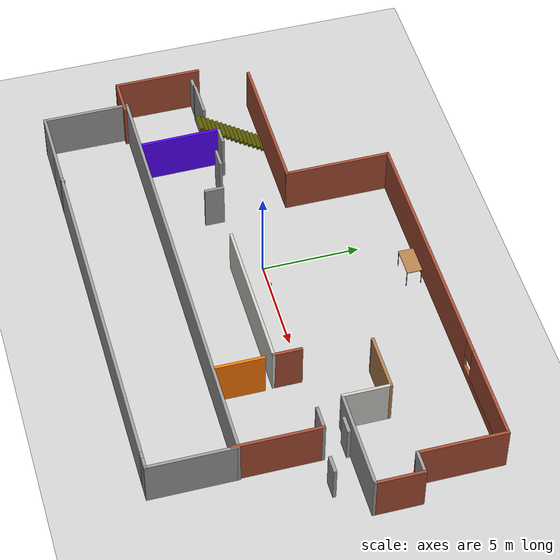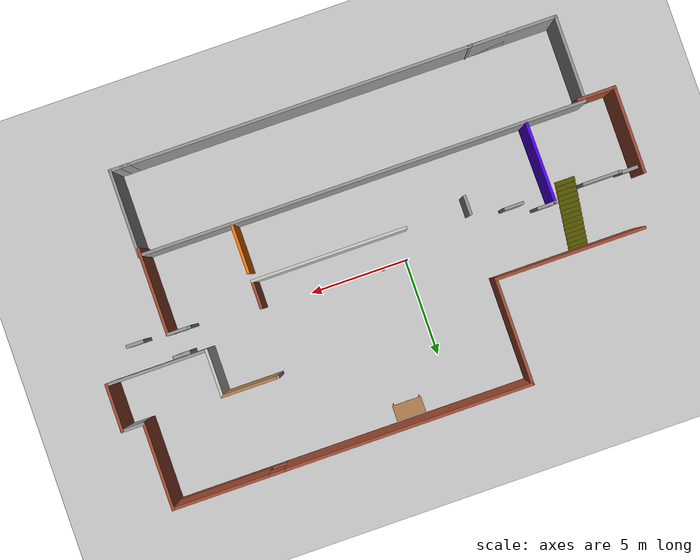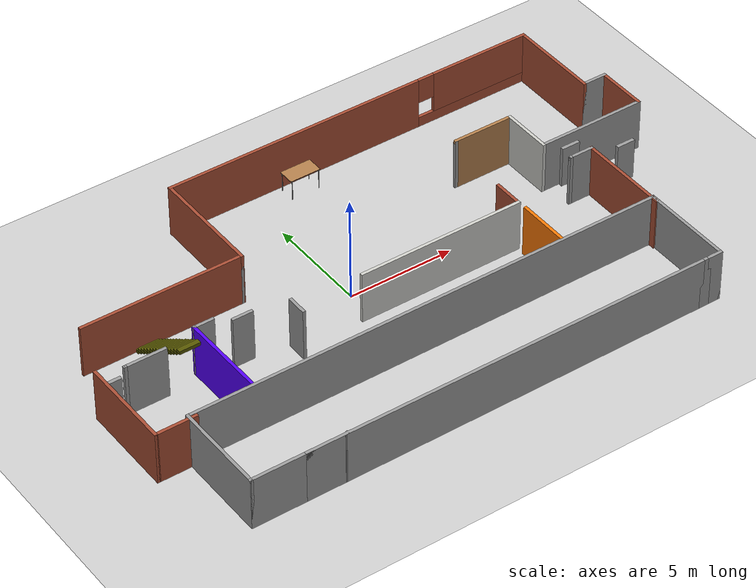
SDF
<sdf version="1.6">
 <world name="default">
  <plugin name="welcome" filename="libwelcome.so"/>
  <light name="sun" type="directional">
   <pose>0 0 10 0 -0 0</pose>
   <diffuse>0.8 0.8 0.8 1</diffuse>
   <specular>0.2 0.2 0.2 1</specular>
   <attenuation>
    <range>1000</range>
    <constant>0.9</constant>
    <linear>0.01</linear>
    <quadratic>0.001</quadratic>
   </attenuation>
   <direction>-0.5 0.1 -0.9</direction>
  </light>
  <model name="ground_plane">
   <static>1</static>
   <link name="link">
    <collision name="collision">
     <geometry><plane><normal>0 0 1</normal><size>100 100</size></plane></geometry>
     <surface>
      <contact><collide_bitmask>65535</collide_bitmask></contact>
      <friction><ode><mu>100</mu><mu2>50</mu2></ode></friction>
     </surface>
    </collision>
    <visual name="visual">
     <cast_shadows>0</cast_shadows>
     <geometry><plane><normal>0 0 1</normal><size>100 100</size></plane></geometry>
     <material>
      <script><uri>file://media/materials/scripts/gazebo.material</uri><name>Gazebo/Grey</name></script>
     </material>
    </visual>
   </link>
  </model>
  <gravity>0 0 -9.8</gravity>
  <magnetic_field>6e-06 2.3e-05 -4.2e-05</magnetic_field>
  <atmosphere type="adiabatic"/>
  <physics name="default_physics" default="0" type="ode">
   <max_step_size>0.001</max_step_size>
   <real_time_factor>1</real_time_factor>
   <real_time_update_rate>1000</real_time_update_rate>
  </physics>
  <scene><ambient>0.4 0.4 0.4 1</ambient><background>0.7 0.7 0.7 1</background><shadows>1</shadows></scene>
  <spherical_coordinates>
   <surface_model>EARTH_WGS84</surface_model>
   <latitude_deg>0</latitude_deg>
   <longitude_deg>0</longitude_deg>
   <elevation>0</elevation>
   <heading_deg>0</heading_deg>
  </spherical_coordinates>
  <model name="table">
   <static>1</static>
   <link name="link">
    <collision name="surface">
     <pose>0 0 1 0 -0 0</pose>
     <geometry><box><size>1.5 0.8 0.03</size></box></geometry>
     <surface><friction><ode><mu>0.6</mu><mu2>0.6</mu2></ode></friction></surface>
    </collision>
    <visual name="visual1">
     <pose>0 0 1 0 -0 0</pose>
     <geometry><box><size>1.5 0.8 0.03</size></box></geometry>
     <material>
      <script><uri>file://media/materials/scripts/gazebo.material</uri><name>Gazebo/Wood</name></script>
     </material>
    </visual>
    <collision name="front_left_leg">
     <pose>0.68 0.38 0.5 0 -0 0</pose>
     <geometry><cylinder><radius>0.02</radius><length>1</length></cylinder></geometry>
    </collision>
    <visual name="front_left_leg">
     <pose>0.68 0.38 0.5 0 -0 0</pose>
     <geometry><cylinder><radius>0.02</radius><length>1</length></cylinder></geometry>
     <material>
      <script><uri>file://media/materials/scripts/gazebo.material</uri><name>Gazebo/Grey</name></script>
     </material>
    </visual>
    <collision name="front_right_leg">
     <pose>0.68 -0.38 0.5 0 -0 0</pose>
     <geometry><cylinder><radius>0.02</radius><length>1</length></cylinder></geometry>
    </collision>
    <visual name="front_right_leg">
     <pose>0.68 -0.38 0.5 0 -0 0</pose>
     <geometry><cylinder><radius>0.02</radius><length>1</length></cylinder></geometry>
     <material>
      <script><uri>file://media/materials/scripts/gazebo.material</uri><name>Gazebo/Grey</name></script>
     </material>
    </visual>
    <collision name="back_right_leg">
     <pose>-0.68 -0.38 0.5 0 -0 0</pose>
     <geometry><cylinder><radius>0.02</radius><length>1</length></cylinder></geometry>
    </collision>
    <visual name="back_right_leg">
     <pose>-0.68 -0.38 0.5 0 -0 0</pose>
     <geometry><cylinder><radius>0.02</radius><length>1</length></cylinder></geometry>
     <material>
      <script><uri>file://media/materials/scripts/gazebo.material</uri><name>Gazebo/Grey</name></script>
     </material>
    </visual>
    <collision name="back_left_leg">
     <pose>-0.68 0.38 0.5 0 -0 0</pose>
     <geometry><cylinder><radius>0.02</radius><length>1</length></cylinder></geometry>
    </collision>
    <visual name="back_left_leg">
     <pose>-0.68 0.38 0.5 0 -0 0</pose>
     <geometry><cylinder><radius>0.02</radius><length>1</length></cylinder></geometry>
     <material>
      <script><uri>file://media/materials/scripts/gazebo.material</uri><name>Gazebo/Grey</name></script>
     </material>
    </visual>
   </link>
   <pose>2.2685 6.9934 0 0 -0 0</pose>
  </model>
  <model name="my_ball">
   <link name="link">
    <inertial>
     <mass>1</mass>
     <inertia><ixx>0.1</ixx><ixy>0</ixy><ixz>0</ixz><iyy>0.1</iyy><iyz>0</iyz><izz>0.1</izz></inertia>
    </inertial>
    <visual name="visual">
     <geometry><sphere><radius>0.1</radius></sphere></geometry>
     <material>
      <script><name>Gazebo/Grey</name><uri>file://media/materials/scripts/gazebo.material</uri></script>
      <shader type="pixel"><normal_map>__default__</normal_map></shader>
      <ambient>1 1 1 1</ambient>
      <diffuse>1 1 1 1</diffuse>
      <specular>1 1 1 1</specular>
      <emissive>1 1 1 1</emissive>
     </material>
    </visual>
    <collision name="collision">
     <geometry><sphere><radius>0.1</radius></sphere></geometry>
     <surface>
      <friction>
       <ode><mu>1</mu><mu2>1</mu2><fdir1>0 0 0</fdir1><slip1>0</slip1><slip2>0</slip2></ode>
       <torsional>
        <coefficient>1</coefficient>
        <patch_radius>0</patch_radius>
        <surface_radius>0</surface_radius>
        <use_patch_radius>1</use_patch_radius>
        <ode><slip>0</slip></ode>
       </torsional>
      </friction>
      <bounce><restitution_coefficient>0</restitution_coefficient><threshold>1e+06</threshold></bounce>
      <contact>
       <collide_without_contact>0</collide_without_contact>
       <collide_without_contact_bitmask>1</collide_without_contact_bitmask>
       <collide_bitmask>1</collide_bitmask>
       <ode>
        <soft_cfm>0</soft_cfm>
        <soft_erp>0.2</soft_erp>
        <kp>1e+13</kp>
        <kd>1</kd>
        <max_vel>0.01</max_vel>
        <min_depth>0</min_depth>
       </ode>
       <bullet>
        <split_impulse>1</split_impulse>
        <split_impulse_penetration_threshold>-0.01</split_impulse_penetration_threshold>
        <soft_cfm>0</soft_cfm>
        <soft_erp>0.2</soft_erp>
        <kp>1e+13</kp>
        <kd>1</kd>
       </bullet>
      </contact>
     </surface>
    </collision>
   </link>
   <static>0</static>
   <pose>1.2011 0.032789 0.1 0 -0 0</pose>
  </model>
  <model name="homeOffice">
   <link name="Door_2">
    <pose>10.1664 -0.686476 0 0 -0 0</pose>
    <visual name="Door_2_Visual">
     <pose>0 0 1 0 -0 0</pose>
     <geometry><box><size>0.9 0.17 2</size></box></geometry>
     <material>
      <script><uri>file://media/materials/scripts/gazebo.material</uri><name>Gazebo/Grey</name></script>
      <shader type="pixel"/>
      <ambient>0.3 0.3 0.3 1</ambient>
      <diffuse>0.7 0.7 0.7 1</diffuse>
      <specular>0.01 0.01 0.01 1</specular>
      <emissive>0 0 0 1</emissive>
     </material>
    </visual>
    <collision name="Door_2_Collision">
     <pose>0 0 1 0 -0 0</pose>
     <geometry><box><size>0.9 0.17 2</size></box></geometry>
     <surface>
      <friction>
       <ode><mu>1</mu><mu2>1</mu2><fdir1>0 0 0</fdir1><slip1>0</slip1><slip2>0</slip2></ode>
       <torsional>
        <coefficient>1</coefficient>
        <patch_radius>0</patch_radius>
        <surface_radius>0</surface_radius>
        <use_patch_radius>1</use_patch_radius>
        <ode><slip>0</slip></ode>
       </torsional>
      </friction>
      <bounce><restitution_coefficient>0</restitution_coefficient><threshold>1e+06</threshold></bounce>
      <contact>
       <collide_without_contact>0</collide_without_contact>
       <collide_without_contact_bitmask>1</collide_without_contact_bitmask>
       <collide_bitmask>1</collide_bitmask>
       <ode>
        <soft_cfm>0</soft_cfm>
        <soft_erp>0.2</soft_erp>
        <kp>1e+13</kp>
        <kd>1</kd>
        <max_vel>0.01</max_vel>
        <min_depth>0</min_depth>
       </ode>
       <bullet>
        <split_impulse>1</split_impulse>
        <split_impulse_penetration_threshold>-0.01</split_impulse_penetration_threshold>
        <soft_cfm>0</soft_cfm>
        <soft_erp>0.2</soft_erp>
        <kp>1e+13</kp>
        <kd>1</kd>
       </bullet>
      </contact>
     </surface>
    </collision>
   </link>
   <link name="Door_3">
    <pose>-13.5001 -2.06196 0 0 -0 0</pose>
    <visual name="Door_3_Visual">
     <pose>0 0 1 0 -0 0</pose>
     <geometry><box><size>0.9 0.17 2</size></box></geometry>
     <material>
      <script><uri>file://media/materials/scripts/gazebo.material</uri><name>Gazebo/Grey</name></script>
      <shader type="pixel"/>
      <ambient>0.3 0.3 0.3 1</ambient>
      <diffuse>0.7 0.7 0.7 1</diffuse>
      <specular>0.01 0.01 0.01 1</specular>
      <emissive>0 0 0 1</emissive>
     </material>
    </visual>
    <collision name="Door_3_Collision">
     <pose>0 0 1 0 -0 0</pose>
     <geometry><box><size>0.9 0.17 2</size></box></geometry>
     <surface>
      <friction>
       <ode><mu>1</mu><mu2>1</mu2><fdir1>0 0 0</fdir1><slip1>0</slip1><slip2>0</slip2></ode>
       <torsional>
        <coefficient>1</coefficient>
        <patch_radius>0</patch_radius>
        <surface_radius>0</surface_radius>
        <use_patch_radius>1</use_patch_radius>
        <ode><slip>0</slip></ode>
       </torsional>
      </friction>
      <bounce><restitution_coefficient>0</restitution_coefficient><threshold>1e+06</threshold></bounce>
      <contact>
       <collide_without_contact>0</collide_without_contact>
       <collide_without_contact_bitmask>1</collide_without_contact_bitmask>
       <collide_bitmask>1</collide_bitmask>
       <ode>
        <soft_cfm>0</soft_cfm>
        <soft_erp>0.2</soft_erp>
        <kp>1e+13</kp>
        <kd>1</kd>
        <max_vel>0.01</max_vel>
        <min_depth>0</min_depth>
       </ode>
       <bullet>
        <split_impulse>1</split_impulse>
        <split_impulse_penetration_threshold>-0.01</split_impulse_penetration_threshold>
        <soft_cfm>0</soft_cfm>
        <soft_erp>0.2</soft_erp>
        <kp>1e+13</kp>
        <kd>1</kd>
       </bullet>
      </contact>
     </surface>
    </collision>
   </link>
   <link name="Door_4">
    <pose>12.1488 -1.9406 0 0 -0 0</pose>
    <visual name="Door_4_Visual">
     <pose>0 0 1 0 -0 0</pose>
     <geometry><box><size>0.9 0.17 2</size></box></geometry>
     <material>
      <script><uri>file://media/materials/scripts/gazebo.material</uri><name>Gazebo/Grey</name></script>
      <shader type="pixel"/>
      <ambient>0.3 0.3 0.3 1</ambient>
      <diffuse>0.7 0.7 0.7 1</diffuse>
      <specular>0.01 0.01 0.01 1</specular>
      <emissive>0 0 0 1</emissive>
     </material>
    </visual>
    <collision name="Door_4_Collision">
     <pose>0 0 1 0 -0 0</pose>
     <geometry><box><size>0.9 0.17 2</size></box></geometry>
     <surface>
      <friction>
       <ode><mu>1</mu><mu2>1</mu2><fdir1>0 0 0</fdir1><slip1>0</slip1><slip2>0</slip2></ode>
       <torsional>
        <coefficient>1</coefficient>
        <patch_radius>0</patch_radius>
        <surface_radius>0</surface_radius>
        <use_patch_radius>1</use_patch_radius>
        <ode><slip>0</slip></ode>
       </torsional>
      </friction>
      <bounce><restitution_coefficient>0</restitution_coefficient><threshold>1e+06</threshold></bounce>
      <contact>
       <collide_without_contact>0</collide_without_contact>
       <collide_without_contact_bitmask>1</collide_without_contact_bitmask>
       <collide_bitmask>1</collide_bitmask>
       <ode>
        <soft_cfm>0</soft_cfm>
        <soft_erp>0.2</soft_erp>
        <kp>1e+13</kp>
        <kd>1</kd>
        <max_vel>0.01</max_vel>
        <min_depth>0</min_depth>
       </ode>
       <bullet>
        <split_impulse>1</split_impulse>
        <split_impulse_penetration_threshold>-0.01</split_impulse_penetration_threshold>
        <soft_cfm>0</soft_cfm>
        <soft_erp>0.2</soft_erp>
        <kp>1e+13</kp>
        <kd>1</kd>
       </bullet>
      </contact>
     </surface>
    </collision>
   </link>
   <link name="Stairs_2">
    <visual name="Stairs_2_Visual_2">
     <pose>-10.1827 0.277913 0.416667 0 -0 0</pose>
     <geometry><box><size>1 0.233333 0.166667</size></box></geometry>
     <material>
      <script><uri>file://media/materials/scripts/gazebo.material</uri><name>Gazebo/Grey</name></script>
      <ambient>0.333333 0.333333 0 1</ambient>
      <shader type="pixel"/>
      <diffuse>0.7 0.7 0.7 1</diffuse>
      <specular>0.01 0.01 0.01 1</specular>
      <emissive>0 0 0 1</emissive>
     </material>
     <meta><layer>0</layer></meta>
    </visual>
    <visual name="Stairs_2_Visual_0">
     <pose>-10.1827 0.74458 0.083333 0 -0 0</pose>
     <geometry><box><size>1 0.233333 0.166667</size></box></geometry>
     <material>
      <script><uri>file://media/materials/scripts/gazebo.material</uri><name>Gazebo/Grey</name></script>
      <ambient>0.333333 0.333333 0 1</ambient>
      <shader type="pixel"/>
      <diffuse>0.7 0.7 0.7 1</diffuse>
      <specular>0.01 0.01 0.01 1</specular>
      <emissive>0 0 0 1</emissive>
     </material>
     <meta><layer>0</layer></meta>
    </visual>
    <visual name="Stairs_2_Visual_1">
     <pose>-10.1827 0.511247 0.25 0 -0 0</pose>
     <geometry><box><size>1 0.233333 0.166667</size></box></geometry>
     <material>
      <script><uri>file://media/materials/scripts/gazebo.material</uri><name>Gazebo/Grey</name></script>
      <ambient>0.333333 0.333333 0 1</ambient>
      <shader type="pixel"/>
      <diffuse>0.7 0.7 0.7 1</diffuse>
      <specular>0.01 0.01 0.01 1</specular>
      <emissive>0 0 0 1</emissive>
     </material>
     <meta><layer>0</layer></meta>
    </visual>
    <visual name="Stairs_2_Visual_3">
     <pose>-10.1827 0.04458 0.583333 0 -0 0</pose>
     <geometry><box><size>1 0.233333 0.166667</size></box></geometry>
     <material>
      <script><uri>file://media/materials/scripts/gazebo.material</uri><name>Gazebo/Grey</name></script>
      <ambient>0.333333 0.333333 0 1</ambient>
      <shader type="pixel"/>
      <diffuse>0.7 0.7 0.7 1</diffuse>
      <specular>0.01 0.01 0.01 1</specular>
      <emissive>0 0 0 1</emissive>
     </material>
     <meta><layer>0</layer></meta>
    </visual>
    <visual name="Stairs_2_Visual_4">
     <pose>-10.1827 -0.188753 0.75 0 -0 0</pose>
     <geometry><box><size>1 0.233333 0.166667</size></box></geometry>
     <material>
      <script><uri>file://media/materials/scripts/gazebo.material</uri><name>Gazebo/Grey</name></script>
      <ambient>0.333333 0.333333 0 1</ambient>
      <shader type="pixel"/>
      <diffuse>0.7 0.7 0.7 1</diffuse>
      <specular>0.01 0.01 0.01 1</specular>
      <emissive>0 0 0 1</emissive>
     </material>
     <meta><layer>0</layer></meta>
    </visual>
    <visual name="Stairs_2_Visual_5">
     <pose>-10.1827 -0.422087 0.916667 0 -0 0</pose>
     <geometry><box><size>1 0.233333 0.166667</size></box></geometry>
     <material>
      <script><uri>file://media/materials/scripts/gazebo.material</uri><name>Gazebo/Grey</name></script>
      <ambient>0.333333 0.333333 0 1</ambient>
      <shader type="pixel"/>
      <diffuse>0.7 0.7 0.7 1</diffuse>
      <specular>0.01 0.01 0.01 1</specular>
      <emissive>0 0 0 1</emissive>
     </material>
     <meta><layer>0</layer></meta>
    </visual>
    <visual name="Stairs_2_Visual_6">
     <pose>-10.1827 -0.65542 1.08333 0 -0 0</pose>
     <geometry><box><size>1 0.233333 0.166667</size></box></geometry>
     <material>
      <script><uri>file://media/materials/scripts/gazebo.material</uri><name>Gazebo/Grey</name></script>
      <ambient>0.333333 0.333333 0 1</ambient>
      <shader type="pixel"/>
      <diffuse>0.7 0.7 0.7 1</diffuse>
      <specular>0.01 0.01 0.01 1</specular>
      <emissive>0 0 0 1</emissive>
     </material>
     <meta><layer>0</layer></meta>
    </visual>
    <visual name="Stairs_2_Visual_7">
     <pose>-10.1827 -0.888753 1.25 0 -0 0</pose>
     <geometry><box><size>1 0.233333 0.166667</size></box></geometry>
     <material>
      <script><uri>file://media/materials/scripts/gazebo.material</uri><name>Gazebo/Grey</name></script>
      <ambient>0.333333 0.333333 0 1</ambient>
      <shader type="pixel"/>
      <diffuse>0.7 0.7 0.7 1</diffuse>
      <specular>0.01 0.01 0.01 1</specular>
      <emissive>0 0 0 1</emissive>
     </material>
     <meta><layer>0</layer></meta>
    </visual>
    <visual name="Stairs_2_Visual_8">
     <pose>-10.1827 -1.12209 1.41667 0 -0 0</pose>
     <geometry><box><size>1 0.233333 0.166667</size></box></geometry>
     <material>
      <script><uri>file://media/materials/scripts/gazebo.material</uri><name>Gazebo/Grey</name></script>
      <ambient>0.333333 0.333333 0 1</ambient>
      <shader type="pixel"/>
      <diffuse>0.7 0.7 0.7 1</diffuse>
      <specular>0.01 0.01 0.01 1</specular>
      <emissive>0 0 0 1</emissive>
     </material>
     <meta><layer>0</layer></meta>
    </visual>
    <visual name="Stairs_2_Visual_9">
     <pose>-10.1827 -1.35542 1.58333 0 -0 0</pose>
     <geometry><box><size>1 0.233333 0.166667</size></box></geometry>
     <material>
      <script><uri>file://media/materials/scripts/gazebo.material</uri><name>Gazebo/Grey</name></script>
      <ambient>0.333333 0.333333 0 1</ambient>
      <shader type="pixel"/>
      <diffuse>0.7 0.7 0.7 1</diffuse>
      <specular>0.01 0.01 0.01 1</specular>
      <emissive>0 0 0 1</emissive>
     </material>
     <meta><layer>0</layer></meta>
    </visual>
    <visual name="Stairs_2_Visual_10">
     <pose>-10.1827 -1.58875 1.75 0 -0 0</pose>
     <geometry><box><size>1 0.233333 0.166667</size></box></geometry>
     <material>
      <script><uri>file://media/materials/scripts/gazebo.material</uri><name>Gazebo/Grey</name></script>
      <ambient>0.333333 0.333333 0 1</ambient>
      <shader type="pixel"/>
      <diffuse>0.7 0.7 0.7 1</diffuse>
      <specular>0.01 0.01 0.01 1</specular>
      <emissive>0 0 0 1</emissive>
     </material>
     <meta><layer>0</layer></meta>
    </visual>
    <visual name="Stairs_2_Visual_11">
     <pose>-10.1827 -1.82209 1.91667 0 -0 0</pose>
     <geometry><box><size>1 0.233333 0.166667</size></box></geometry>
     <material>
      <script><uri>file://media/materials/scripts/gazebo.material</uri><name>Gazebo/Grey</name></script>
      <ambient>0.333333 0.333333 0 1</ambient>
      <shader type="pixel"/>
      <diffuse>0.7 0.7 0.7 1</diffuse>
      <specular>0.01 0.01 0.01 1</specular>
      <emissive>0 0 0 1</emissive>
     </material>
     <meta><layer>0</layer></meta>
    </visual>
    <visual name="Stairs_2_Visual_12">
     <pose>-10.1827 -2.05542 2.08333 0 -0 0</pose>
     <geometry><box><size>1 0.233333 0.166667</size></box></geometry>
     <material>
      <script><uri>file://media/materials/scripts/gazebo.material</uri><name>Gazebo/Grey</name></script>
      <ambient>0.333333 0.333333 0 1</ambient>
      <shader type="pixel"/>
      <diffuse>0.7 0.7 0.7 1</diffuse>
      <specular>0.01 0.01 0.01 1</specular>
      <emissive>0 0 0 1</emissive>
     </material>
     <meta><layer>0</layer></meta>
    </visual>
    <visual name="Stairs_2_Visual_13">
     <pose>-10.1827 -2.28875 2.25 0 -0 0</pose>
     <geometry><box><size>1 0.233333 0.166667</size></box></geometry>
     <material>
      <script><uri>file://media/materials/scripts/gazebo.material</uri><name>Gazebo/Grey</name></script>
      <ambient>0.333333 0.333333 0 1</ambient>
      <shader type="pixel"/>
      <diffuse>0.7 0.7 0.7 1</diffuse>
      <specular>0.01 0.01 0.01 1</specular>
      <emissive>0 0 0 1</emissive>
     </material>
     <meta><layer>0</layer></meta>
    </visual>
    <visual name="Stairs_2_Visual_14">
     <pose>-10.1827 -2.52209 2.41667 0 -0 0</pose>
     <geometry><box><size>1 0.233333 0.166667</size></box></geometry>
     <material>
      <script><uri>file://media/materials/scripts/gazebo.material</uri><name>Gazebo/Grey</name></script>
      <ambient>0.333333 0.333333 0 1</ambient>
      <shader type="pixel"/>
      <diffuse>0.7 0.7 0.7 1</diffuse>
      <specular>0.01 0.01 0.01 1</specular>
      <emissive>0 0 0 1</emissive>
     </material>
     <meta><layer>0</layer></meta>
    </visual>
    <collision name="Stairs_2_Collision_0">
     <pose>-10.1827 0.74458 0.083333 0 -0 0</pose>
     <geometry><box><size>1 0.233333 0.166667</size></box></geometry>
     <surface>
      <friction>
       <ode><mu>1</mu><mu2>1</mu2><fdir1>0 0 0</fdir1><slip1>0</slip1><slip2>0</slip2></ode>
       <torsional>
        <coefficient>1</coefficient>
        <patch_radius>0</patch_radius>
        <surface_radius>0</surface_radius>
        <use_patch_radius>1</use_patch_radius>
        <ode><slip>0</slip></ode>
       </torsional>
      </friction>
      <bounce><restitution_coefficient>0</restitution_coefficient><threshold>1e+06</threshold></bounce>
      <contact>
       <collide_without_contact>0</collide_without_contact>
       <collide_without_contact_bitmask>1</collide_without_contact_bitmask>
       <collide_bitmask>1</collide_bitmask>
       <ode>
        <soft_cfm>0</soft_cfm>
        <soft_erp>0.2</soft_erp>
        <kp>1e+13</kp>
        <kd>1</kd>
        <max_vel>0.01</max_vel>
        <min_depth>0</min_depth>
       </ode>
       <bullet>
        <split_impulse>1</split_impulse>
        <split_impulse_penetration_threshold>-0.01</split_impulse_penetration_threshold>
        <soft_cfm>0</soft_cfm>
        <soft_erp>0.2</soft_erp>
        <kp>1e+13</kp>
        <kd>1</kd>
       </bullet>
      </contact>
     </surface>
    </collision>
    <collision name="Stairs_2_Collision_1">
     <pose>-10.1827 0.511247 0.25 0 -0 0</pose>
     <geometry><box><size>1 0.233333 0.166667</size></box></geometry>
     <surface>
      <friction>
       <ode><mu>1</mu><mu2>1</mu2><fdir1>0 0 0</fdir1><slip1>0</slip1><slip2>0</slip2></ode>
       <torsional>
        <coefficient>1</coefficient>
        <patch_radius>0</patch_radius>
        <surface_radius>0</surface_radius>
        <use_patch_radius>1</use_patch_radius>
        <ode><slip>0</slip></ode>
       </torsional>
      </friction>
      <bounce><restitution_coefficient>0</restitution_coefficient><threshold>1e+06</threshold></bounce>
      <contact>
       <collide_without_contact>0</collide_without_contact>
       <collide_without_contact_bitmask>1</collide_without_contact_bitmask>
       <collide_bitmask>1</collide_bitmask>
       <ode>
        <soft_cfm>0</soft_cfm>
        <soft_erp>0.2</soft_erp>
        <kp>1e+13</kp>
        <kd>1</kd>
        <max_vel>0.01</max_vel>
        <min_depth>0</min_depth>
       </ode>
       <bullet>
        <split_impulse>1</split_impulse>
        <split_impulse_penetration_threshold>-0.01</split_impulse_penetration_threshold>
        <soft_cfm>0</soft_cfm>
        <soft_erp>0.2</soft_erp>
        <kp>1e+13</kp>
        <kd>1</kd>
       </bullet>
      </contact>
     </surface>
    </collision>
    <collision name="Stairs_2_Collision_2">
     <pose>-10.1827 0.277913 0.416667 0 -0 0</pose>
     <geometry><box><size>1 0.233333 0.166667</size></box></geometry>
     <surface>
      <friction>
       <ode><mu>1</mu><mu2>1</mu2><fdir1>0 0 0</fdir1><slip1>0</slip1><slip2>0</slip2></ode>
       <torsional>
        <coefficient>1</coefficient>
        <patch_radius>0</patch_radius>
        <surface_radius>0</surface_radius>
        <use_patch_radius>1</use_patch_radius>
        <ode><slip>0</slip></ode>
       </torsional>
      </friction>
      <bounce><restitution_coefficient>0</restitution_coefficient><threshold>1e+06</threshold></bounce>
      <contact>
       <collide_without_contact>0</collide_without_contact>
       <collide_without_contact_bitmask>1</collide_without_contact_bitmask>
       <collide_bitmask>1</collide_bitmask>
       <ode>
        <soft_cfm>0</soft_cfm>
        <soft_erp>0.2</soft_erp>
        <kp>1e+13</kp>
        <kd>1</kd>
        <max_vel>0.01</max_vel>
        <min_depth>0</min_depth>
       </ode>
       <bullet>
        <split_impulse>1</split_impulse>
        <split_impulse_penetration_threshold>-0.01</split_impulse_penetration_threshold>
        <soft_cfm>0</soft_cfm>
        <soft_erp>0.2</soft_erp>
        <kp>1e+13</kp>
        <kd>1</kd>
       </bullet>
      </contact>
     </surface>
    </collision>
    <collision name="Stairs_2_Collision_3">
     <pose>-10.1827 0.04458 0.583333 0 -0 0</pose>
     <geometry><box><size>1 0.233333 0.166667</size></box></geometry>
     <surface>
      <friction>
       <ode><mu>1</mu><mu2>1</mu2><fdir1>0 0 0</fdir1><slip1>0</slip1><slip2>0</slip2></ode>
       <torsional>
        <coefficient>1</coefficient>
        <patch_radius>0</patch_radius>
        <surface_radius>0</surface_radius>
        <use_patch_radius>1</use_patch_radius>
        <ode><slip>0</slip></ode>
       </torsional>
      </friction>
      <bounce><restitution_coefficient>0</restitution_coefficient><threshold>1e+06</threshold></bounce>
      <contact>
       <collide_without_contact>0</collide_without_contact>
       <collide_without_contact_bitmask>1</collide_without_contact_bitmask>
       <collide_bitmask>1</collide_bitmask>
       <ode>
        <soft_cfm>0</soft_cfm>
        <soft_erp>0.2</soft_erp>
        <kp>1e+13</kp>
        <kd>1</kd>
        <max_vel>0.01</max_vel>
        <min_depth>0</min_depth>
       </ode>
       <bullet>
        <split_impulse>1</split_impulse>
        <split_impulse_penetration_threshold>-0.01</split_impulse_penetration_threshold>
        <soft_cfm>0</soft_cfm>
        <soft_erp>0.2</soft_erp>
        <kp>1e+13</kp>
        <kd>1</kd>
       </bullet>
      </contact>
     </surface>
    </collision>
    <collision name="Stairs_2_Collision_4">
     <pose>-10.1827 -0.188753 0.75 0 -0 0</pose>
     <geometry><box><size>1 0.233333 0.166667</size></box></geometry>
     <surface>
      <friction>
       <ode><mu>1</mu><mu2>1</mu2><fdir1>0 0 0</fdir1><slip1>0</slip1><slip2>0</slip2></ode>
       <torsional>
        <coefficient>1</coefficient>
        <patch_radius>0</patch_radius>
        <surface_radius>0</surface_radius>
        <use_patch_radius>1</use_patch_radius>
        <ode><slip>0</slip></ode>
       </torsional>
      </friction>
      <bounce><restitution_coefficient>0</restitution_coefficient><threshold>1e+06</threshold></bounce>
      <contact>
       <collide_without_contact>0</collide_without_contact>
       <collide_without_contact_bitmask>1</collide_without_contact_bitmask>
       <collide_bitmask>1</collide_bitmask>
       <ode>
        <soft_cfm>0</soft_cfm>
        <soft_erp>0.2</soft_erp>
        <kp>1e+13</kp>
        <kd>1</kd>
        <max_vel>0.01</max_vel>
        <min_depth>0</min_depth>
       </ode>
       <bullet>
        <split_impulse>1</split_impulse>
        <split_impulse_penetration_threshold>-0.01</split_impulse_penetration_threshold>
        <soft_cfm>0</soft_cfm>
        <soft_erp>0.2</soft_erp>
        <kp>1e+13</kp>
        <kd>1</kd>
       </bullet>
      </contact>
     </surface>
    </collision>
    <collision name="Stairs_2_Collision_6">
     <pose>-10.1827 -0.65542 1.08333 0 -0 0</pose>
     <geometry><box><size>1 0.233333 0.166667</size></box></geometry>
     <surface>
      <friction>
       <ode><mu>1</mu><mu2>1</mu2><fdir1>0 0 0</fdir1><slip1>0</slip1><slip2>0</slip2></ode>
       <torsional>
        <coefficient>1</coefficient>
        <patch_radius>0</patch_radius>
        <surface_radius>0</surface_radius>
        <use_patch_radius>1</use_patch_radius>
        <ode><slip>0</slip></ode>
       </torsional>
      </friction>
      <bounce><restitution_coefficient>0</restitution_coefficient><threshold>1e+06</threshold></bounce>
      <contact>
       <collide_without_contact>0</collide_without_contact>
       <collide_without_contact_bitmask>1</collide_without_contact_bitmask>
       <collide_bitmask>1</collide_bitmask>
       <ode>
        <soft_cfm>0</soft_cfm>
        <soft_erp>0.2</soft_erp>
        <kp>1e+13</kp>
        <kd>1</kd>
        <max_vel>0.01</max_vel>
        <min_depth>0</min_depth>
       </ode>
       <bullet>
        <split_impulse>1</split_impulse>
        <split_impulse_penetration_threshold>-0.01</split_impulse_penetration_threshold>
        <soft_cfm>0</soft_cfm>
        <soft_erp>0.2</soft_erp>
        <kp>1e+13</kp>
        <kd>1</kd>
       </bullet>
      </contact>
     </surface>
    </collision>
    <collision name="Stairs_2_Collision_5">
     <pose>-10.1827 -0.422087 0.916667 0 -0 0</pose>
     <geometry><box><size>1 0.233333 0.166667</size></box></geometry>
     <surface>
      <friction>
       <ode><mu>1</mu><mu2>1</mu2><fdir1>0 0 0</fdir1><slip1>0</slip1><slip2>0</slip2></ode>
       <torsional>
        <coefficient>1</coefficient>
        <patch_radius>0</patch_radius>
        <surface_radius>0</surface_radius>
        <use_patch_radius>1</use_patch_radius>
        <ode><slip>0</slip></ode>
       </torsional>
      </friction>
      <bounce><restitution_coefficient>0</restitution_coefficient><threshold>1e+06</threshold></bounce>
      <contact>
       <collide_without_contact>0</collide_without_contact>
       <collide_without_contact_bitmask>1</collide_without_contact_bitmask>
       <collide_bitmask>1</collide_bitmask>
       <ode>
        <soft_cfm>0</soft_cfm>
        <soft_erp>0.2</soft_erp>
        <kp>1e+13</kp>
        <kd>1</kd>
        <max_vel>0.01</max_vel>
        <min_depth>0</min_depth>
       </ode>
       <bullet>
        <split_impulse>1</split_impulse>
        <split_impulse_penetration_threshold>-0.01</split_impulse_penetration_threshold>
        <soft_cfm>0</soft_cfm>
        <soft_erp>0.2</soft_erp>
        <kp>1e+13</kp>
        <kd>1</kd>
       </bullet>
      </contact>
     </surface>
    </collision>
    <collision name="Stairs_2_Collision_7">
     <pose>-10.1827 -0.888753 1.25 0 -0 0</pose>
     <geometry><box><size>1 0.233333 0.166667</size></box></geometry>
     <surface>
      <friction>
       <ode><mu>1</mu><mu2>1</mu2><fdir1>0 0 0</fdir1><slip1>0</slip1><slip2>0</slip2></ode>
       <torsional>
        <coefficient>1</coefficient>
        <patch_radius>0</patch_radius>
        <surface_radius>0</surface_radius>
        <use_patch_radius>1</use_patch_radius>
        <ode><slip>0</slip></ode>
       </torsional>
      </friction>
      <bounce><restitution_coefficient>0</restitution_coefficient><threshold>1e+06</threshold></bounce>
      <contact>
       <collide_without_contact>0</collide_without_contact>
       <collide_without_contact_bitmask>1</collide_without_contact_bitmask>
       <collide_bitmask>1</collide_bitmask>
       <ode>
        <soft_cfm>0</soft_cfm>
        <soft_erp>0.2</soft_erp>
        <kp>1e+13</kp>
        <kd>1</kd>
        <max_vel>0.01</max_vel>
        <min_depth>0</min_depth>
       </ode>
       <bullet>
        <split_impulse>1</split_impulse>
        <split_impulse_penetration_threshold>-0.01</split_impulse_penetration_threshold>
        <soft_cfm>0</soft_cfm>
        <soft_erp>0.2</soft_erp>
        <kp>1e+13</kp>
        <kd>1</kd>
       </bullet>
      </contact>
     </surface>
    </collision>
    <collision name="Stairs_2_Collision_8">
     <pose>-10.1827 -1.12209 1.41667 0 -0 0</pose>
     <geometry><box><size>1 0.233333 0.166667</size></box></geometry>
     <surface>
      <friction>
       <ode><mu>1</mu><mu2>1</mu2><fdir1>0 0 0</fdir1><slip1>0</slip1><slip2>0</slip2></ode>
       <torsional>
        <coefficient>1</coefficient>
        <patch_radius>0</patch_radius>
        <surface_radius>0</surface_radius>
        <use_patch_radius>1</use_patch_radius>
        <ode><slip>0</slip></ode>
       </torsional>
      </friction>
      <bounce><restitution_coefficient>0</restitution_coefficient><threshold>1e+06</threshold></bounce>
      <contact>
       <collide_without_contact>0</collide_without_contact>
       <collide_without_contact_bitmask>1</collide_without_contact_bitmask>
       <collide_bitmask>1</collide_bitmask>
       <ode>
        <soft_cfm>0</soft_cfm>
        <soft_erp>0.2</soft_erp>
        <kp>1e+13</kp>
        <kd>1</kd>
        <max_vel>0.01</max_vel>
        <min_depth>0</min_depth>
       </ode>
       <bullet>
        <split_impulse>1</split_impulse>
        <split_impulse_penetration_threshold>-0.01</split_impulse_penetration_threshold>
        <soft_cfm>0</soft_cfm>
        <soft_erp>0.2</soft_erp>
        <kp>1e+13</kp>
        <kd>1</kd>
       </bullet>
      </contact>
     </surface>
    </collision>
    <collision name="Stairs_2_Collision_9">
     <pose>-10.1827 -1.35542 1.58333 0 -0 0</pose>
     <geometry><box><size>1 0.233333 0.166667</size></box></geometry>
     <surface>
      <friction>
       <ode><mu>1</mu><mu2>1</mu2><fdir1>0 0 0</fdir1><slip1>0</slip1><slip2>0</slip2></ode>
       <torsional>
        <coefficient>1</coefficient>
        <patch_radius>0</patch_radius>
        <surface_radius>0</surface_radius>
        <use_patch_radius>1</use_patch_radius>
        <ode><slip>0</slip></ode>
       </torsional>
      </friction>
      <bounce><restitution_coefficient>0</restitution_coefficient><threshold>1e+06</threshold></bounce>
      <contact>
       <collide_without_contact>0</collide_without_contact>
       <collide_without_contact_bitmask>1</collide_without_contact_bitmask>
       <collide_bitmask>1</collide_bitmask>
       <ode>
        <soft_cfm>0</soft_cfm>
        <soft_erp>0.2</soft_erp>
        <kp>1e+13</kp>
        <kd>1</kd>
        <max_vel>0.01</max_vel>
        <min_depth>0</min_depth>
       </ode>
       <bullet>
        <split_impulse>1</split_impulse>
        <split_impulse_penetration_threshold>-0.01</split_impulse_penetration_threshold>
        <soft_cfm>0</soft_cfm>
        <soft_erp>0.2</soft_erp>
        <kp>1e+13</kp>
        <kd>1</kd>
       </bullet>
      </contact>
     </surface>
    </collision>
    <collision name="Stairs_2_Collision_11">
     <pose>-10.1827 -1.82209 1.91667 0 -0 0</pose>
     <geometry><box><size>1 0.233333 0.166667</size></box></geometry>
     <surface>
      <friction>
       <ode><mu>1</mu><mu2>1</mu2><fdir1>0 0 0</fdir1><slip1>0</slip1><slip2>0</slip2></ode>
       <torsional>
        <coefficient>1</coefficient>
        <patch_radius>0</patch_radius>
        <surface_radius>0</surface_radius>
        <use_patch_radius>1</use_patch_radius>
        <ode><slip>0</slip></ode>
       </torsional>
      </friction>
      <bounce><restitution_coefficient>0</restitution_coefficient><threshold>1e+06</threshold></bounce>
      <contact>
       <collide_without_contact>0</collide_without_contact>
       <collide_without_contact_bitmask>1</collide_without_contact_bitmask>
       <collide_bitmask>1</collide_bitmask>
       <ode>
        <soft_cfm>0</soft_cfm>
        <soft_erp>0.2</soft_erp>
        <kp>1e+13</kp>
        <kd>1</kd>
        <max_vel>0.01</max_vel>
        <min_depth>0</min_depth>
       </ode>
       <bullet>
        <split_impulse>1</split_impulse>
        <split_impulse_penetration_threshold>-0.01</split_impulse_penetration_threshold>
        <soft_cfm>0</soft_cfm>
        <soft_erp>0.2</soft_erp>
        <kp>1e+13</kp>
        <kd>1</kd>
       </bullet>
      </contact>
     </surface>
    </collision>
    <collision name="Stairs_2_Collision_10">
     <pose>-10.1827 -1.58875 1.75 0 -0 0</pose>
     <geometry><box><size>1 0.233333 0.166667</size></box></geometry>
     <surface>
      <friction>
       <ode><mu>1</mu><mu2>1</mu2><fdir1>0 0 0</fdir1><slip1>0</slip1><slip2>0</slip2></ode>
       <torsional>
        <coefficient>1</coefficient>
        <patch_radius>0</patch_radius>
        <surface_radius>0</surface_radius>
        <use_patch_radius>1</use_patch_radius>
        <ode><slip>0</slip></ode>
       </torsional>
      </friction>
      <bounce><restitution_coefficient>0</restitution_coefficient><threshold>1e+06</threshold></bounce>
      <contact>
       <collide_without_contact>0</collide_without_contact>
       <collide_without_contact_bitmask>1</collide_without_contact_bitmask>
       <collide_bitmask>1</collide_bitmask>
       <ode>
        <soft_cfm>0</soft_cfm>
        <soft_erp>0.2</soft_erp>
        <kp>1e+13</kp>
        <kd>1</kd>
        <max_vel>0.01</max_vel>
        <min_depth>0</min_depth>
       </ode>
       <bullet>
        <split_impulse>1</split_impulse>
        <split_impulse_penetration_threshold>-0.01</split_impulse_penetration_threshold>
        <soft_cfm>0</soft_cfm>
        <soft_erp>0.2</soft_erp>
        <kp>1e+13</kp>
        <kd>1</kd>
       </bullet>
      </contact>
     </surface>
    </collision>
    <collision name="Stairs_2_Collision_12">
     <pose>-10.1827 -2.05542 2.08333 0 -0 0</pose>
     <geometry><box><size>1 0.233333 0.166667</size></box></geometry>
     <surface>
      <friction>
       <ode><mu>1</mu><mu2>1</mu2><fdir1>0 0 0</fdir1><slip1>0</slip1><slip2>0</slip2></ode>
       <torsional>
        <coefficient>1</coefficient>
        <patch_radius>0</patch_radius>
        <surface_radius>0</surface_radius>
        <use_patch_radius>1</use_patch_radius>
        <ode><slip>0</slip></ode>
       </torsional>
      </friction>
      <bounce><restitution_coefficient>0</restitution_coefficient><threshold>1e+06</threshold></bounce>
      <contact>
       <collide_without_contact>0</collide_without_contact>
       <collide_without_contact_bitmask>1</collide_without_contact_bitmask>
       <collide_bitmask>1</collide_bitmask>
       <ode>
        <soft_cfm>0</soft_cfm>
        <soft_erp>0.2</soft_erp>
        <kp>1e+13</kp>
        <kd>1</kd>
        <max_vel>0.01</max_vel>
        <min_depth>0</min_depth>
       </ode>
       <bullet>
        <split_impulse>1</split_impulse>
        <split_impulse_penetration_threshold>-0.01</split_impulse_penetration_threshold>
        <soft_cfm>0</soft_cfm>
        <soft_erp>0.2</soft_erp>
        <kp>1e+13</kp>
        <kd>1</kd>
       </bullet>
      </contact>
     </surface>
    </collision>
    <collision name="Stairs_2_Collision_13">
     <pose>-10.1827 -2.28875 2.25 0 -0 0</pose>
     <geometry><box><size>1 0.233333 0.166667</size></box></geometry>
     <surface>
      <friction>
       <ode><mu>1</mu><mu2>1</mu2><fdir1>0 0 0</fdir1><slip1>0</slip1><slip2>0</slip2></ode>
       <torsional>
        <coefficient>1</coefficient>
        <patch_radius>0</patch_radius>
        <surface_radius>0</surface_radius>
        <use_patch_radius>1</use_patch_radius>
        <ode><slip>0</slip></ode>
       </torsional>
      </friction>
      <bounce><restitution_coefficient>0</restitution_coefficient><threshold>1e+06</threshold></bounce>
      <contact>
       <collide_without_contact>0</collide_without_contact>
       <collide_without_contact_bitmask>1</collide_without_contact_bitmask>
       <collide_bitmask>1</collide_bitmask>
       <ode>
        <soft_cfm>0</soft_cfm>
        <soft_erp>0.2</soft_erp>
        <kp>1e+13</kp>
        <kd>1</kd>
        <max_vel>0.01</max_vel>
        <min_depth>0</min_depth>
       </ode>
       <bullet>
        <split_impulse>1</split_impulse>
        <split_impulse_penetration_threshold>-0.01</split_impulse_penetration_threshold>
        <soft_cfm>0</soft_cfm>
        <soft_erp>0.2</soft_erp>
        <kp>1e+13</kp>
        <kd>1</kd>
       </bullet>
      </contact>
     </surface>
    </collision>
    <collision name="Stairs_2_Collision_14">
     <pose>-10.1827 -2.52209 2.41667 0 -0 0</pose>
     <geometry><box><size>1 0.233333 0.166667</size></box></geometry>
     <surface>
      <friction>
       <ode><mu>1</mu><mu2>1</mu2><fdir1>0 0 0</fdir1><slip1>0</slip1><slip2>0</slip2></ode>
       <torsional>
        <coefficient>1</coefficient>
        <patch_radius>0</patch_radius>
        <surface_radius>0</surface_radius>
        <use_patch_radius>1</use_patch_radius>
        <ode><slip>0</slip></ode>
       </torsional>
      </friction>
      <bounce><restitution_coefficient>0</restitution_coefficient><threshold>1e+06</threshold></bounce>
      <contact>
       <collide_without_contact>0</collide_without_contact>
       <collide_without_contact_bitmask>1</collide_without_contact_bitmask>
       <collide_bitmask>1</collide_bitmask>
       <ode>
        <soft_cfm>0</soft_cfm>
        <soft_erp>0.2</soft_erp>
        <kp>1e+13</kp>
        <kd>1</kd>
        <max_vel>0.01</max_vel>
        <min_depth>0</min_depth>
       </ode>
       <bullet>
        <split_impulse>1</split_impulse>
        <split_impulse_penetration_threshold>-0.01</split_impulse_penetration_threshold>
        <soft_cfm>0</soft_cfm>
        <soft_erp>0.2</soft_erp>
        <kp>1e+13</kp>
        <kd>1</kd>
       </bullet>
      </contact>
     </surface>
    </collision>
   </link>
   <link name="Wall_11">
    <pose>-5.36279 -2.9996 0 0 0 -1.5708</pose>
    <visual name="Wall_11_Visual">
     <pose>0 0 1.25 0 -0 0</pose>
     <geometry><box><size>1 0.15 2.5</size></box></geometry>
     <material>
      <script><uri>file://media/materials/scripts/gazebo.material</uri><name>Gazebo/Grey</name></script>
      <ambient>1 1 1 1</ambient>
      <shader type="pixel"/>
      <diffuse>0.7 0.7 0.7 1</diffuse>
      <specular>0.01 0.01 0.01 1</specular>
      <emissive>0 0 0 1</emissive>
     </material>
     <meta><layer>0</layer></meta>
    </visual>
    <collision name="Wall_11_Collision">
     <pose>0 0 1.25 0 -0 0</pose>
     <geometry><box><size>1 0.15 2.5</size></box></geometry>
     <surface>
      <friction>
       <ode><mu>1</mu><mu2>1</mu2><fdir1>0 0 0</fdir1><slip1>0</slip1><slip2>0</slip2></ode>
       <torsional>
        <coefficient>1</coefficient>
        <patch_radius>0</patch_radius>
        <surface_radius>0</surface_radius>
        <use_patch_radius>1</use_patch_radius>
        <ode><slip>0</slip></ode>
       </torsional>
      </friction>
      <bounce><restitution_coefficient>0</restitution_coefficient><threshold>1e+06</threshold></bounce>
      <contact>
       <collide_without_contact>0</collide_without_contact>
       <collide_without_contact_bitmask>1</collide_without_contact_bitmask>
       <collide_bitmask>1</collide_bitmask>
       <ode>
        <soft_cfm>0</soft_cfm>
        <soft_erp>0.2</soft_erp>
        <kp>1e+13</kp>
        <kd>1</kd>
        <max_vel>0.01</max_vel>
        <min_depth>0</min_depth>
       </ode>
       <bullet>
        <split_impulse>1</split_impulse>
        <split_impulse_penetration_threshold>-0.01</split_impulse_penetration_threshold>
        <soft_cfm>0</soft_cfm>
        <soft_erp>0.2</soft_erp>
        <kp>1e+13</kp>
        <kd>1</kd>
       </bullet>
      </contact>
     </surface>
    </collision>
   </link>
   <link name="Wall_13">
    <pose>5.73721 -4.5996 0 0 0 -1.5708</pose>
    <visual name="Wall_13_Visual">
     <pose>0 0 1.25 0 -0 0</pose>
     <geometry><box><size>2.5 0.15 2.5</size></box></geometry>
     <material>
      <script><uri>file://media/materials/scripts/gazebo.material</uri><name>Gazebo/Grey</name></script>
      <ambient>0.996078 0.47451 0.0196078 1</ambient>
      <shader type="pixel"/>
      <diffuse>0.7 0.7 0.7 1</diffuse>
      <specular>0.01 0.01 0.01 1</specular>
      <emissive>0 0 0 1</emissive>
     </material>
     <meta><layer>0</layer></meta>
    </visual>
    <collision name="Wall_13_Collision">
     <pose>0 0 1.25 0 -0 0</pose>
     <geometry><box><size>2.5 0.15 2.5</size></box></geometry>
     <surface>
      <friction>
       <ode><mu>1</mu><mu2>1</mu2><fdir1>0 0 0</fdir1><slip1>0</slip1><slip2>0</slip2></ode>
       <torsional>
        <coefficient>1</coefficient>
        <patch_radius>0</patch_radius>
        <surface_radius>0</surface_radius>
        <use_patch_radius>1</use_patch_radius>
        <ode><slip>0</slip></ode>
       </torsional>
      </friction>
      <bounce><restitution_coefficient>0</restitution_coefficient><threshold>1e+06</threshold></bounce>
      <contact>
       <collide_without_contact>0</collide_without_contact>
       <collide_without_contact_bitmask>1</collide_without_contact_bitmask>
       <collide_bitmask>1</collide_bitmask>
       <ode>
        <soft_cfm>0</soft_cfm>
        <soft_erp>0.2</soft_erp>
        <kp>1e+13</kp>
        <kd>1</kd>
        <max_vel>0.01</max_vel>
        <min_depth>0</min_depth>
       </ode>
       <bullet>
        <split_impulse>1</split_impulse>
        <split_impulse_penetration_threshold>-0.01</split_impulse_penetration_threshold>
        <soft_cfm>0</soft_cfm>
        <soft_erp>0.2</soft_erp>
        <kp>1e+13</kp>
        <kd>1</kd>
       </bullet>
      </contact>
     </surface>
    </collision>
   </link>
   <link name="Wall_15">
    <pose>-9.38779 -3.7496 0 0 -0 1.58314</pose>
    <visual name="Wall_15_Visual">
     <pose>0 0 1.25 0 -0 0</pose>
     <geometry><box><size>4.20031 0.15 2.5</size></box></geometry>
     <material>
      <script><uri>file://media/materials/scripts/gazebo.material</uri><name>Gazebo/Grey</name></script>
      <ambient>0.333333 0 1 1</ambient>
      <shader type="pixel"/>
      <diffuse>0.7 0.7 0.7 1</diffuse>
      <specular>0.01 0.01 0.01 1</specular>
      <emissive>0 0 0 1</emissive>
     </material>
     <meta><layer>0</layer></meta>
    </visual>
    <collision name="Wall_15_Collision">
     <pose>0 0 1.25 0 -0 0</pose>
     <geometry><box><size>4.20031 0.15 2.5</size></box></geometry>
     <surface>
      <friction>
       <ode><mu>1</mu><mu2>1</mu2><fdir1>0 0 0</fdir1><slip1>0</slip1><slip2>0</slip2></ode>
       <torsional>
        <coefficient>1</coefficient>
        <patch_radius>0</patch_radius>
        <surface_radius>0</surface_radius>
        <use_patch_radius>1</use_patch_radius>
        <ode><slip>0</slip></ode>
       </torsional>
      </friction>
      <bounce><restitution_coefficient>0</restitution_coefficient><threshold>1e+06</threshold></bounce>
      <contact>
       <collide_without_contact>0</collide_without_contact>
       <collide_without_contact_bitmask>1</collide_without_contact_bitmask>
       <collide_bitmask>1</collide_bitmask>
       <ode>
        <soft_cfm>0</soft_cfm>
        <soft_erp>0.2</soft_erp>
        <kp>1e+13</kp>
        <kd>1</kd>
        <max_vel>0.01</max_vel>
        <min_depth>0</min_depth>
       </ode>
       <bullet>
        <split_impulse>1</split_impulse>
        <split_impulse_penetration_threshold>-0.01</split_impulse_penetration_threshold>
        <soft_cfm>0</soft_cfm>
        <soft_erp>0.2</soft_erp>
        <kp>1e+13</kp>
        <kd>1</kd>
       </bullet>
      </contact>
     </surface>
    </collision>
   </link>
   <link name="Wall_16">
    <pose>-9.41279 -1.7246 0 0 -0 0</pose>
    <visual name="Wall_16_Visual">
     <pose>0 0 1.25 0 -0 0</pose>
     <geometry><box><size>0.15 0.15 2.5</size></box></geometry>
     <material>
      <script><uri>file://media/materials/scripts/gazebo.material</uri><name>Gazebo/Grey</name></script>
      <ambient>1 1 1 1</ambient>
      <shader type="pixel"/>
      <diffuse>0.7 0.7 0.7 1</diffuse>
      <specular>0.01 0.01 0.01 1</specular>
      <emissive>0 0 0 1</emissive>
     </material>
     <meta><layer>0</layer></meta>
    </visual>
    <collision name="Wall_16_Collision">
     <pose>0 0 1.25 0 -0 0</pose>
     <geometry><box><size>0.15 0.15 2.5</size></box></geometry>
     <surface>
      <friction>
       <ode><mu>1</mu><mu2>1</mu2><fdir1>0 0 0</fdir1><slip1>0</slip1><slip2>0</slip2></ode>
       <torsional>
        <coefficient>1</coefficient>
        <patch_radius>0</patch_radius>
        <surface_radius>0</surface_radius>
        <use_patch_radius>1</use_patch_radius>
        <ode><slip>0</slip></ode>
       </torsional>
      </friction>
      <bounce><restitution_coefficient>0</restitution_coefficient><threshold>1e+06</threshold></bounce>
      <contact>
       <collide_without_contact>0</collide_without_contact>
       <collide_without_contact_bitmask>1</collide_without_contact_bitmask>
       <collide_bitmask>1</collide_bitmask>
       <ode>
        <soft_cfm>0</soft_cfm>
        <soft_erp>0.2</soft_erp>
        <kp>1e+13</kp>
        <kd>1</kd>
        <max_vel>0.01</max_vel>
        <min_depth>0</min_depth>
       </ode>
       <bullet>
        <split_impulse>1</split_impulse>
        <split_impulse_penetration_threshold>-0.01</split_impulse_penetration_threshold>
        <soft_cfm>0</soft_cfm>
        <soft_erp>0.2</soft_erp>
        <kp>1e+13</kp>
        <kd>1</kd>
       </bullet>
      </contact>
     </surface>
    </collision>
   </link>
   <link name="Wall_20">
    <pose>5.69721 -2.2696 0 0 0 -1.5708</pose>
    <visual name="Wall_20_Visual">
     <pose>0 0 1.25 0 -0 0</pose>
     <geometry><box><size>1.5 0.15 2.5</size></box></geometry>
     <material>
      <script><uri>file://media/materials/scripts/gazebo.material</uri><name>Gazebo/Bricks</name></script>
      <ambient>1 1 1 1</ambient>
      <shader type="pixel"/>
      <diffuse>1 1 1 1</diffuse>
      <specular>0.2 0.2 0.2 1</specular>
      <emissive>0 0 0 1</emissive>
     </material>
     <meta><layer>0</layer></meta>
    </visual>
    <collision name="Wall_20_Collision">
     <pose>0 0 1.25 0 -0 0</pose>
     <geometry><box><size>1.5 0.15 2.5</size></box></geometry>
     <surface>
      <friction>
       <ode><mu>1</mu><mu2>1</mu2><fdir1>0 0 0</fdir1><slip1>0</slip1><slip2>0</slip2></ode>
       <torsional>
        <coefficient>1</coefficient>
        <patch_radius>0</patch_radius>
        <surface_radius>0</surface_radius>
        <use_patch_radius>1</use_patch_radius>
        <ode><slip>0</slip></ode>
       </torsional>
      </friction>
      <bounce><restitution_coefficient>0</restitution_coefficient><threshold>1e+06</threshold></bounce>
      <contact>
       <collide_without_contact>0</collide_without_contact>
       <collide_without_contact_bitmask>1</collide_without_contact_bitmask>
       <collide_bitmask>1</collide_bitmask>
       <ode>
        <soft_cfm>0</soft_cfm>
        <soft_erp>0.2</soft_erp>
        <kp>1e+13</kp>
        <kd>1</kd>
        <max_vel>0.01</max_vel>
        <min_depth>0</min_depth>
       </ode>
       <bullet>
        <split_impulse>1</split_impulse>
        <split_impulse_penetration_threshold>-0.01</split_impulse_penetration_threshold>
        <soft_cfm>0</soft_cfm>
        <soft_erp>0.2</soft_erp>
        <kp>1e+13</kp>
        <kd>1</kd>
       </bullet>
      </contact>
     </surface>
    </collision>
   </link>
   <link name="Wall_21">
    <pose>1.77221 -2.9446 0 0 -0 3.14159</pose>
    <visual name="Wall_21_Visual">
     <pose>0 0 1.25 0 -0 0</pose>
     <geometry><box><size>8 0.15 2.5</size></box></geometry>
     <material>
      <script><uri>file://media/materials/scripts/gazebo.material</uri><name>Gazebo/CeilingTiled</name></script>
      <ambient>0.435294 0.796078 0.67451 1</ambient>
      <shader type="pixel"/>
      <diffuse>1 1 1 1</diffuse>
      <specular>0 0 0 1</specular>
      <emissive>0 0 0 1</emissive>
     </material>
     <meta><layer>0</layer></meta>
    </visual>
    <collision name="Wall_21_Collision">
     <pose>0 0 1.25 0 -0 0</pose>
     <geometry><box><size>8 0.15 2.5</size></box></geometry>
     <surface>
      <friction>
       <ode><mu>1</mu><mu2>1</mu2><fdir1>0 0 0</fdir1><slip1>0</slip1><slip2>0</slip2></ode>
       <torsional>
        <coefficient>1</coefficient>
        <patch_radius>0</patch_radius>
        <surface_radius>0</surface_radius>
        <use_patch_radius>1</use_patch_radius>
        <ode><slip>0</slip></ode>
       </torsional>
      </friction>
      <bounce><restitution_coefficient>0</restitution_coefficient><threshold>1e+06</threshold></bounce>
      <contact>
       <collide_without_contact>0</collide_without_contact>
       <collide_without_contact_bitmask>1</collide_without_contact_bitmask>
       <collide_bitmask>1</collide_bitmask>
       <ode>
        <soft_cfm>0</soft_cfm>
        <soft_erp>0.2</soft_erp>
        <kp>1e+13</kp>
        <kd>1</kd>
        <max_vel>0.01</max_vel>
        <min_depth>0</min_depth>
       </ode>
       <bullet>
        <split_impulse>1</split_impulse>
        <split_impulse_penetration_threshold>-0.01</split_impulse_penetration_threshold>
        <soft_cfm>0</soft_cfm>
        <soft_erp>0.2</soft_erp>
        <kp>1e+13</kp>
        <kd>1</kd>
       </bullet>
      </contact>
     </surface>
    </collision>
   </link>
   <link name="Wall_27">
    <pose>-7.46779 -2.2246 0 0 -0 3.14159</pose>
    <visual name="Wall_27_Visual">
     <pose>0 0 1.25 0 -0 0</pose>
     <geometry><box><size>1 0.15 2.5</size></box></geometry>
     <material>
      <script><uri>file://media/materials/scripts/gazebo.material</uri><name>Gazebo/Grey</name></script>
      <ambient>1 1 1 1</ambient>
      <shader type="pixel"/>
      <diffuse>0.7 0.7 0.7 1</diffuse>
      <specular>0.01 0.01 0.01 1</specular>
      <emissive>0 0 0 1</emissive>
     </material>
     <meta><layer>0</layer></meta>
    </visual>
    <collision name="Wall_27_Collision">
     <pose>0 0 1.25 0 -0 0</pose>
     <geometry><box><size>1 0.15 2.5</size></box></geometry>
     <surface>
      <friction>
       <ode><mu>1</mu><mu2>1</mu2><fdir1>0 0 0</fdir1><slip1>0</slip1><slip2>0</slip2></ode>
       <torsional>
        <coefficient>1</coefficient>
        <patch_radius>0</patch_radius>
        <surface_radius>0</surface_radius>
        <use_patch_radius>1</use_patch_radius>
        <ode><slip>0</slip></ode>
       </torsional>
      </friction>
      <bounce><restitution_coefficient>0</restitution_coefficient><threshold>1e+06</threshold></bounce>
      <contact>
       <collide_without_contact>0</collide_without_contact>
       <collide_without_contact_bitmask>1</collide_without_contact_bitmask>
       <collide_bitmask>1</collide_bitmask>
       <ode>
        <soft_cfm>0</soft_cfm>
        <soft_erp>0.2</soft_erp>
        <kp>1e+13</kp>
        <kd>1</kd>
        <max_vel>0.01</max_vel>
        <min_depth>0</min_depth>
       </ode>
       <bullet>
        <split_impulse>1</split_impulse>
        <split_impulse_penetration_threshold>-0.01</split_impulse_penetration_threshold>
        <soft_cfm>0</soft_cfm>
        <soft_erp>0.2</soft_erp>
        <kp>1e+13</kp>
        <kd>1</kd>
       </bullet>
      </contact>
     </surface>
    </collision>
   </link>
   <link name="Wall_3">
    <pose>-8.98779 -1.7246 0 0 -0 0</pose>
    <visual name="Wall_3_Visual">
     <pose>0 0 1.25 0 -0 0</pose>
     <geometry><box><size>1 0.15 2.5</size></box></geometry>
     <material>
      <script><uri>file://media/materials/scripts/gazebo.material</uri><name>Gazebo/Grey</name></script>
      <ambient>1 1 1 1</ambient>
      <shader type="pixel"/>
      <diffuse>0.7 0.7 0.7 1</diffuse>
      <specular>0.01 0.01 0.01 1</specular>
      <emissive>0 0 0 1</emissive>
     </material>
     <meta><layer>0</layer></meta>
    </visual>
    <collision name="Wall_3_Collision">
     <pose>0 0 1.25 0 -0 0</pose>
     <geometry><box><size>1 0.15 2.5</size></box></geometry>
     <surface>
      <friction>
       <ode><mu>1</mu><mu2>1</mu2><fdir1>0 0 0</fdir1><slip1>0</slip1><slip2>0</slip2></ode>
       <torsional>
        <coefficient>1</coefficient>
        <patch_radius>0</patch_radius>
        <surface_radius>0</surface_radius>
        <use_patch_radius>1</use_patch_radius>
        <ode><slip>0</slip></ode>
       </torsional>
      </friction>
      <bounce><restitution_coefficient>0</restitution_coefficient><threshold>1e+06</threshold></bounce>
      <contact>
       <collide_without_contact>0</collide_without_contact>
       <collide_without_contact_bitmask>1</collide_without_contact_bitmask>
       <collide_bitmask>1</collide_bitmask>
       <ode>
        <soft_cfm>0</soft_cfm>
        <soft_erp>0.2</soft_erp>
        <kp>1e+13</kp>
        <kd>1</kd>
        <max_vel>0.01</max_vel>
        <min_depth>0</min_depth>
       </ode>
       <bullet>
        <split_impulse>1</split_impulse>
        <split_impulse_penetration_threshold>-0.01</split_impulse_penetration_threshold>
        <soft_cfm>0</soft_cfm>
        <soft_erp>0.2</soft_erp>
        <kp>1e+13</kp>
        <kd>1</kd>
       </bullet>
      </contact>
     </surface>
    </collision>
   </link>
   <link name="Wall_47">
    <pose>10.3872 -4.0196 0 0 -0 1.5708</pose>
    <visual name="Wall_47_Visual">
     <pose>0 0 1.25 0 -0 0</pose>
     <geometry><box><size>4.5 0.15 2.5</size></box></geometry>
     <material>
      <script><uri>file://media/materials/scripts/gazebo.material</uri><name>Gazebo/Bricks</name></script>
      <ambient>1 1 1 1</ambient>
      <shader type="pixel"/>
      <diffuse>1 1 1 1</diffuse>
      <specular>0.2 0.2 0.2 1</specular>
      <emissive>0 0 0 1</emissive>
     </material>
     <meta><layer>0</layer></meta>
    </visual>
    <collision name="Wall_47_Collision">
     <pose>0 0 1.25 0 -0 0</pose>
     <geometry><box><size>4.5 0.15 2.5</size></box></geometry>
     <surface>
      <friction>
       <ode><mu>1</mu><mu2>1</mu2><fdir1>0 0 0</fdir1><slip1>0</slip1><slip2>0</slip2></ode>
       <torsional>
        <coefficient>1</coefficient>
        <patch_radius>0</patch_radius>
        <surface_radius>0</surface_radius>
        <use_patch_radius>1</use_patch_radius>
        <ode><slip>0</slip></ode>
       </torsional>
      </friction>
      <bounce><restitution_coefficient>0</restitution_coefficient><threshold>1e+06</threshold></bounce>
      <contact>
       <collide_without_contact>0</collide_without_contact>
       <collide_without_contact_bitmask>1</collide_without_contact_bitmask>
       <collide_bitmask>1</collide_bitmask>
       <ode>
        <soft_cfm>0</soft_cfm>
        <soft_erp>0.2</soft_erp>
        <kp>1e+13</kp>
        <kd>1</kd>
        <max_vel>0.01</max_vel>
        <min_depth>0</min_depth>
       </ode>
       <bullet>
        <split_impulse>1</split_impulse>
        <split_impulse_penetration_threshold>-0.01</split_impulse_penetration_threshold>
        <soft_cfm>0</soft_cfm>
        <soft_erp>0.2</soft_erp>
        <kp>1e+13</kp>
        <kd>1</kd>
       </bullet>
      </contact>
     </surface>
    </collision>
   </link>
   <link name="Wall_48">
    <pose>9.83721 -1.8446 0 0 -0 3.14159</pose>
    <visual name="Wall_48_Visual">
     <pose>0 0 1.25 0 -0 0</pose>
     <geometry><box><size>1.25 0.15 2.5</size></box></geometry>
     <material>
      <script><uri>file://media/materials/scripts/gazebo.material</uri><name>Gazebo/Grey</name></script>
      <ambient>1 1 1 1</ambient>
      <shader type="pixel"/>
      <diffuse>0.7 0.7 0.7 1</diffuse>
      <specular>0.01 0.01 0.01 1</specular>
      <emissive>0 0 0 1</emissive>
     </material>
     <meta><layer>0</layer></meta>
    </visual>
    <collision name="Wall_48_Collision">
     <pose>0 0 1.25 0 -0 0</pose>
     <geometry><box><size>1.25 0.15 2.5</size></box></geometry>
     <surface>
      <friction>
       <ode><mu>1</mu><mu2>1</mu2><fdir1>0 0 0</fdir1><slip1>0</slip1><slip2>0</slip2></ode>
       <torsional>
        <coefficient>1</coefficient>
        <patch_radius>0</patch_radius>
        <surface_radius>0</surface_radius>
        <use_patch_radius>1</use_patch_radius>
        <ode><slip>0</slip></ode>
       </torsional>
      </friction>
      <bounce><restitution_coefficient>0</restitution_coefficient><threshold>1e+06</threshold></bounce>
      <contact>
       <collide_without_contact>0</collide_without_contact>
       <collide_without_contact_bitmask>1</collide_without_contact_bitmask>
       <collide_bitmask>1</collide_bitmask>
       <ode>
        <soft_cfm>0</soft_cfm>
        <soft_erp>0.2</soft_erp>
        <kp>1e+13</kp>
        <kd>1</kd>
        <max_vel>0.01</max_vel>
        <min_depth>0</min_depth>
       </ode>
       <bullet>
        <split_impulse>1</split_impulse>
        <split_impulse_penetration_threshold>-0.01</split_impulse_penetration_threshold>
        <soft_cfm>0</soft_cfm>
        <soft_erp>0.2</soft_erp>
        <kp>1e+13</kp>
        <kd>1</kd>
       </bullet>
      </contact>
     </surface>
    </collision>
   </link>
   <link name="Wall_49">
    <pose>9.28721 -1.8446 0 0 -0 0</pose>
    <visual name="Wall_49_Visual">
     <pose>0 0 1.25 0 -0 0</pose>
     <geometry><box><size>0.15 0.15 2.5</size></box></geometry>
     <material>
      <script><uri>file://media/materials/scripts/gazebo.material</uri><name>Gazebo/Grey</name></script>
      <ambient>1 1 1 1</ambient>
      <shader type="pixel"/>
      <diffuse>0.7 0.7 0.7 1</diffuse>
      <specular>0.01 0.01 0.01 1</specular>
      <emissive>0 0 0 1</emissive>
     </material>
     <meta><layer>0</layer></meta>
    </visual>
    <collision name="Wall_49_Collision">
     <pose>0 0 1.25 0 -0 0</pose>
     <geometry><box><size>0.15 0.15 2.5</size></box></geometry>
     <surface>
      <friction>
       <ode><mu>1</mu><mu2>1</mu2><fdir1>0 0 0</fdir1><slip1>0</slip1><slip2>0</slip2></ode>
       <torsional>
        <coefficient>1</coefficient>
        <patch_radius>0</patch_radius>
        <surface_radius>0</surface_radius>
        <use_patch_radius>1</use_patch_radius>
        <ode><slip>0</slip></ode>
       </torsional>
      </friction>
      <bounce><restitution_coefficient>0</restitution_coefficient><threshold>1e+06</threshold></bounce>
      <contact>
       <collide_without_contact>0</collide_without_contact>
       <collide_without_contact_bitmask>1</collide_without_contact_bitmask>
       <collide_bitmask>1</collide_bitmask>
       <ode>
        <soft_cfm>0</soft_cfm>
        <soft_erp>0.2</soft_erp>
        <kp>1e+13</kp>
        <kd>1</kd>
        <max_vel>0.01</max_vel>
        <min_depth>0</min_depth>
       </ode>
       <bullet>
        <split_impulse>1</split_impulse>
        <split_impulse_penetration_threshold>-0.01</split_impulse_penetration_threshold>
        <soft_cfm>0</soft_cfm>
        <soft_erp>0.2</soft_erp>
        <kp>1e+13</kp>
        <kd>1</kd>
       </bullet>
      </contact>
     </surface>
    </collision>
   </link>
   <link name="Wall_51">
    <pose>-13.9728 -3.8896 0 0 0 -1.5708</pose>
    <visual name="Wall_51_Visual">
     <pose>0 0 1.25 0 -0 0</pose>
     <geometry><box><size>4.5 0.15 2.5</size></box></geometry>
     <material>
      <script><uri>file://media/materials/scripts/gazebo.material</uri><name>Gazebo/Bricks</name></script>
      <ambient>1 1 1 1</ambient>
      <shader type="pixel"/>
      <diffuse>1 1 1 1</diffuse>
      <specular>0.2 0.2 0.2 1</specular>
      <emissive>0 0 0 1</emissive>
     </material>
     <meta><layer>0</layer></meta>
    </visual>
    <collision name="Wall_51_Collision">
     <pose>0 0 1.25 0 -0 0</pose>
     <geometry><box><size>4.5 0.15 2.5</size></box></geometry>
     <surface>
      <friction>
       <ode><mu>1</mu><mu2>1</mu2><fdir1>0 0 0</fdir1><slip1>0</slip1><slip2>0</slip2></ode>
       <torsional>
        <coefficient>1</coefficient>
        <patch_radius>0</patch_radius>
        <surface_radius>0</surface_radius>
        <use_patch_radius>1</use_patch_radius>
        <ode><slip>0</slip></ode>
       </torsional>
      </friction>
      <bounce><restitution_coefficient>0</restitution_coefficient><threshold>1e+06</threshold></bounce>
      <contact>
       <collide_without_contact>0</collide_without_contact>
       <collide_without_contact_bitmask>1</collide_without_contact_bitmask>
       <collide_bitmask>1</collide_bitmask>
       <ode>
        <soft_cfm>0</soft_cfm>
        <soft_erp>0.2</soft_erp>
        <kp>1e+13</kp>
        <kd>1</kd>
        <max_vel>0.01</max_vel>
        <min_depth>0</min_depth>
       </ode>
       <bullet>
        <split_impulse>1</split_impulse>
        <split_impulse_penetration_threshold>-0.01</split_impulse_penetration_threshold>
        <soft_cfm>0</soft_cfm>
        <soft_erp>0.2</soft_erp>
        <kp>1e+13</kp>
        <kd>1</kd>
       </bullet>
      </contact>
     </surface>
    </collision>
   </link>
   <link name="Wall_52">
    <pose>-13.0478 -6.0646 0 0 -0 0</pose>
    <visual name="Wall_52_Visual">
     <pose>0 0 1.25 0 -0 0</pose>
     <geometry><box><size>2 0.15 2.5</size></box></geometry>
     <material>
      <script><uri>file://media/materials/scripts/gazebo.material</uri><name>Gazebo/Bricks</name></script>
      <ambient>1 1 1 1</ambient>
      <shader type="pixel"/>
      <diffuse>1 1 1 1</diffuse>
      <specular>0.2 0.2 0.2 1</specular>
      <emissive>0 0 0 1</emissive>
     </material>
     <meta><layer>0</layer></meta>
    </visual>
    <collision name="Wall_52_Collision">
     <pose>0 0 1.25 0 -0 0</pose>
     <geometry><box><size>2 0.15 2.5</size></box></geometry>
     <surface>
      <friction>
       <ode><mu>1</mu><mu2>1</mu2><fdir1>0 0 0</fdir1><slip1>0</slip1><slip2>0</slip2></ode>
       <torsional>
        <coefficient>1</coefficient>
        <patch_radius>0</patch_radius>
        <surface_radius>0</surface_radius>
        <use_patch_radius>1</use_patch_radius>
        <ode><slip>0</slip></ode>
       </torsional>
      </friction>
      <bounce><restitution_coefficient>0</restitution_coefficient><threshold>1e+06</threshold></bounce>
      <contact>
       <collide_without_contact>0</collide_without_contact>
       <collide_without_contact_bitmask>1</collide_without_contact_bitmask>
       <collide_bitmask>1</collide_bitmask>
       <ode>
        <soft_cfm>0</soft_cfm>
        <soft_erp>0.2</soft_erp>
        <kp>1e+13</kp>
        <kd>1</kd>
        <max_vel>0.01</max_vel>
        <min_depth>0</min_depth>
       </ode>
       <bullet>
        <split_impulse>1</split_impulse>
        <split_impulse_penetration_threshold>-0.01</split_impulse_penetration_threshold>
        <soft_cfm>0</soft_cfm>
        <soft_erp>0.2</soft_erp>
        <kp>1e+13</kp>
        <kd>1</kd>
       </bullet>
      </contact>
     </surface>
    </collision>
   </link>
   <link name="Wall_56">
    <pose>-11.9478 -2.1146 0 0 -0 3.14159</pose>
    <visual name="Wall_56_Visual">
     <pose>0 0 1.25 0 -0 0</pose>
     <geometry><box><size>2 0.15 2.5</size></box></geometry>
     <material>
      <script><uri>file://media/materials/scripts/gazebo.material</uri><name>Gazebo/Grey</name></script>
      <ambient>1 1 1 1</ambient>
      <shader type="pixel"/>
      <diffuse>0.7 0.7 0.7 1</diffuse>
      <specular>0.01 0.01 0.01 1</specular>
      <emissive>0 0 0 1</emissive>
     </material>
     <meta><layer>0</layer></meta>
    </visual>
    <collision name="Wall_56_Collision">
     <pose>0 0 1.25 0 -0 0</pose>
     <geometry><box><size>2 0.15 2.5</size></box></geometry>
     <surface>
      <friction>
       <ode><mu>1</mu><mu2>1</mu2><fdir1>0 0 0</fdir1><slip1>0</slip1><slip2>0</slip2></ode>
       <torsional>
        <coefficient>1</coefficient>
        <patch_radius>0</patch_radius>
        <surface_radius>0</surface_radius>
        <use_patch_radius>1</use_patch_radius>
        <ode><slip>0</slip></ode>
       </torsional>
      </friction>
      <bounce><restitution_coefficient>0</restitution_coefficient><threshold>1e+06</threshold></bounce>
      <contact>
       <collide_without_contact>0</collide_without_contact>
       <collide_without_contact_bitmask>1</collide_without_contact_bitmask>
       <collide_bitmask>1</collide_bitmask>
       <ode>
        <soft_cfm>0</soft_cfm>
        <soft_erp>0.2</soft_erp>
        <kp>1e+13</kp>
        <kd>1</kd>
        <max_vel>0.01</max_vel>
        <min_depth>0</min_depth>
       </ode>
       <bullet>
        <split_impulse>1</split_impulse>
        <split_impulse_penetration_threshold>-0.01</split_impulse_penetration_threshold>
        <soft_cfm>0</soft_cfm>
        <soft_erp>0.2</soft_erp>
        <kp>1e+13</kp>
        <kd>1</kd>
       </bullet>
      </contact>
     </surface>
    </collision>
   </link>
   <link name="Wall_57">
    <pose>-12.8728 -2.1146 0 0 -0 0</pose>
    <visual name="Wall_57_Visual">
     <pose>0 0 1.25 0 -0 0</pose>
     <geometry><box><size>0.15 0.15 2.5</size></box></geometry>
     <material>
      <script><uri>file://media/materials/scripts/gazebo.material</uri><name>Gazebo/Grey</name></script>
      <ambient>1 1 1 1</ambient>
      <shader type="pixel"/>
      <diffuse>0.7 0.7 0.7 1</diffuse>
      <specular>0.01 0.01 0.01 1</specular>
      <emissive>0 0 0 1</emissive>
     </material>
     <meta><layer>0</layer></meta>
    </visual>
    <collision name="Wall_57_Collision">
     <pose>0 0 1.25 0 -0 0</pose>
     <geometry><box><size>0.15 0.15 2.5</size></box></geometry>
     <surface>
      <friction>
       <ode><mu>1</mu><mu2>1</mu2><fdir1>0 0 0</fdir1><slip1>0</slip1><slip2>0</slip2></ode>
       <torsional>
        <coefficient>1</coefficient>
        <patch_radius>0</patch_radius>
        <surface_radius>0</surface_radius>
        <use_patch_radius>1</use_patch_radius>
        <ode><slip>0</slip></ode>
       </torsional>
      </friction>
      <bounce><restitution_coefficient>0</restitution_coefficient><threshold>1e+06</threshold></bounce>
      <contact>
       <collide_without_contact>0</collide_without_contact>
       <collide_without_contact_bitmask>1</collide_without_contact_bitmask>
       <collide_bitmask>1</collide_bitmask>
       <ode>
        <soft_cfm>0</soft_cfm>
        <soft_erp>0.2</soft_erp>
        <kp>1e+13</kp>
        <kd>1</kd>
        <max_vel>0.01</max_vel>
        <min_depth>0</min_depth>
       </ode>
       <bullet>
        <split_impulse>1</split_impulse>
        <split_impulse_penetration_threshold>-0.01</split_impulse_penetration_threshold>
        <soft_cfm>0</soft_cfm>
        <soft_erp>0.2</soft_erp>
        <kp>1e+13</kp>
        <kd>1</kd>
       </bullet>
      </contact>
     </surface>
    </collision>
   </link>
   <link name="Wall_61">
    <pose>-9.27721 0.8446 0 0 -0 0</pose>
    <visual name="Wall_61_Visual">
     <pose>0 0 1.25 0 -0 0</pose>
     <geometry><box><size>7.75 0.15 2.5</size></box></geometry>
     <material>
      <script><uri>file://media/materials/scripts/gazebo.material</uri><name>Gazebo/Bricks</name></script>
      <ambient>1 1 1 1</ambient>
      <shader type="pixel"/>
      <diffuse>1 1 1 1</diffuse>
      <specular>0.2 0.2 0.2 1</specular>
      <emissive>0 0 0 1</emissive>
     </material>
     <meta><layer>0</layer></meta>
    </visual>
    <collision name="Wall_61_Collision">
     <pose>0 0 1.25 0 -0 0</pose>
     <geometry><box><size>7.75 0.15 2.5</size></box></geometry>
     <surface>
      <friction>
       <ode><mu>1</mu><mu2>1</mu2><fdir1>0 0 0</fdir1><slip1>0</slip1><slip2>0</slip2></ode>
       <torsional>
        <coefficient>1</coefficient>
        <patch_radius>0</patch_radius>
        <surface_radius>0</surface_radius>
        <use_patch_radius>1</use_patch_radius>
        <ode><slip>0</slip></ode>
       </torsional>
      </friction>
      <bounce><restitution_coefficient>0</restitution_coefficient><threshold>1e+06</threshold></bounce>
      <contact>
       <collide_without_contact>0</collide_without_contact>
       <collide_without_contact_bitmask>1</collide_without_contact_bitmask>
       <collide_bitmask>1</collide_bitmask>
       <ode>
        <soft_cfm>0</soft_cfm>
        <soft_erp>0.2</soft_erp>
        <kp>1e+13</kp>
        <kd>1</kd>
        <max_vel>0.01</max_vel>
        <min_depth>0</min_depth>
       </ode>
       <bullet>
        <split_impulse>1</split_impulse>
        <split_impulse_penetration_threshold>-0.01</split_impulse_penetration_threshold>
        <soft_cfm>0</soft_cfm>
        <soft_erp>0.2</soft_erp>
        <kp>1e+13</kp>
        <kd>1</kd>
       </bullet>
      </contact>
     </surface>
    </collision>
   </link>
   <link name="Wall_62">
    <pose>-5.47721 0.8446 0 0 -0 0</pose>
    <visual name="Wall_62_Visual">
     <pose>0 0 1.25 0 -0 0</pose>
     <geometry><box><size>0.15 0.15 2.5</size></box></geometry>
     <material>
      <script><uri>file://media/materials/scripts/gazebo.material</uri><name>Gazebo/Grey</name></script>
      <ambient>1 1 1 1</ambient>
      <shader type="pixel"/>
      <diffuse>0.7 0.7 0.7 1</diffuse>
      <specular>0.01 0.01 0.01 1</specular>
      <emissive>0 0 0 1</emissive>
     </material>
     <meta><layer>0</layer></meta>
    </visual>
    <collision name="Wall_62_Collision">
     <pose>0 0 1.25 0 -0 0</pose>
     <geometry><box><size>0.15 0.15 2.5</size></box></geometry>
     <surface>
      <friction>
       <ode><mu>1</mu><mu2>1</mu2><fdir1>0 0 0</fdir1><slip1>0</slip1><slip2>0</slip2></ode>
       <torsional>
        <coefficient>1</coefficient>
        <patch_radius>0</patch_radius>
        <surface_radius>0</surface_radius>
        <use_patch_radius>1</use_patch_radius>
        <ode><slip>0</slip></ode>
       </torsional>
      </friction>
      <bounce><restitution_coefficient>0</restitution_coefficient><threshold>1e+06</threshold></bounce>
      <contact>
       <collide_without_contact>0</collide_without_contact>
       <collide_without_contact_bitmask>1</collide_without_contact_bitmask>
       <collide_bitmask>1</collide_bitmask>
       <ode>
        <soft_cfm>0</soft_cfm>
        <soft_erp>0.2</soft_erp>
        <kp>1e+13</kp>
        <kd>1</kd>
        <max_vel>0.01</max_vel>
        <min_depth>0</min_depth>
       </ode>
       <bullet>
        <split_impulse>1</split_impulse>
        <split_impulse_penetration_threshold>-0.01</split_impulse_penetration_threshold>
        <soft_cfm>0</soft_cfm>
        <soft_erp>0.2</soft_erp>
        <kp>1e+13</kp>
        <kd>1</kd>
       </bullet>
      </contact>
     </surface>
    </collision>
   </link>
   <link name="Wall_64">
    <pose>-5.47721 3.5196 0 0 -0 1.5708</pose>
    <visual name="Wall_64_Visual">
     <pose>0 0 1.25 0 -0 0</pose>
     <geometry><box><size>5.5 0.15 2.5</size></box></geometry>
     <material>
      <script><uri>file://media/materials/scripts/gazebo.material</uri><name>Gazebo/Bricks</name></script>
      <ambient>1 1 1 1</ambient>
      <shader type="pixel"/>
      <diffuse>1 1 1 1</diffuse>
      <specular>0.2 0.2 0.2 1</specular>
      <emissive>0 0 0 1</emissive>
     </material>
     <meta><layer>0</layer></meta>
    </visual>
    <collision name="Wall_64_Collision">
     <pose>0 0 1.25 0 -0 0</pose>
     <geometry><box><size>5.5 0.15 2.5</size></box></geometry>
     <surface>
      <friction>
       <ode><mu>1</mu><mu2>1</mu2><fdir1>0 0 0</fdir1><slip1>0</slip1><slip2>0</slip2></ode>
       <torsional>
        <coefficient>1</coefficient>
        <patch_radius>0</patch_radius>
        <surface_radius>0</surface_radius>
        <use_patch_radius>1</use_patch_radius>
        <ode><slip>0</slip></ode>
       </torsional>
      </friction>
      <bounce><restitution_coefficient>0</restitution_coefficient><threshold>1e+06</threshold></bounce>
      <contact>
       <collide_without_contact>0</collide_without_contact>
       <collide_without_contact_bitmask>1</collide_without_contact_bitmask>
       <collide_bitmask>1</collide_bitmask>
       <ode>
        <soft_cfm>0</soft_cfm>
        <soft_erp>0.2</soft_erp>
        <kp>1e+13</kp>
        <kd>1</kd>
        <max_vel>0.01</max_vel>
        <min_depth>0</min_depth>
       </ode>
       <bullet>
        <split_impulse>1</split_impulse>
        <split_impulse_penetration_threshold>-0.01</split_impulse_penetration_threshold>
        <soft_cfm>0</soft_cfm>
        <soft_erp>0.2</soft_erp>
        <kp>1e+13</kp>
        <kd>1</kd>
       </bullet>
      </contact>
     </surface>
    </collision>
   </link>
   <link name="Wall_65">
    <pose>3.69779 6.1946 0 0 -0 0</pose>
    <visual name="Wall_65_Visual_0">
     <pose>-2.88525 0 1.25 0 -0 0</pose>
     <geometry><box><size>12.7295 0.15 2.5</size></box></geometry>
     <material>
      <script><uri>file://media/materials/scripts/gazebo.material</uri><name>Gazebo/Bricks</name></script>
      <ambient>1 1 1 1</ambient>
      <shader type="pixel"/>
      <diffuse>1 1 1 1</diffuse>
      <specular>0.2 0.2 0.2 1</specular>
      <emissive>0 0 0 1</emissive>
     </material>
     <meta><layer>0</layer></meta>
    </visual>
    <visual name="Wall_65_Visual_1">
     <pose>6.36475 0 0.25 0 -0 0</pose>
     <geometry><box><size>5.77051 0.15 0.5</size></box></geometry>
     <material>
      <script><uri>file://media/materials/scripts/gazebo.material</uri><name>Gazebo/Bricks</name></script>
      <ambient>1 1 1 1</ambient>
      <shader type="pixel"/>
      <diffuse>1 1 1 1</diffuse>
      <specular>0.2 0.2 0.2 1</specular>
      <emissive>0 0 0 1</emissive>
     </material>
     <meta><layer>0</layer></meta>
    </visual>
    <visual name="Wall_65_Visual_2">
     <pose>6.76475 0 1.5 0 -0 0</pose>
     <geometry><box><size>4.97051 0.15 2</size></box></geometry>
     <material>
      <script><uri>file://media/materials/scripts/gazebo.material</uri><name>Gazebo/Bricks</name></script>
      <ambient>1 1 1 1</ambient>
      <shader type="pixel"/>
      <diffuse>1 1 1 1</diffuse>
      <specular>0.2 0.2 0.2 1</specular>
      <emissive>0 0 0 1</emissive>
     </material>
     <meta><layer>0</layer></meta>
    </visual>
    <visual name="Wall_65_Visual_3">
     <pose>3.87949 0 1.9 0 -0 0</pose>
     <geometry><box><size>0.8 0.15 1.2</size></box></geometry>
     <material>
      <script><uri>file://media/materials/scripts/gazebo.material</uri><name>Gazebo/Bricks</name></script>
      <ambient>1 1 1 1</ambient>
      <shader type="pixel"/>
      <diffuse>1 1 1 1</diffuse>
      <specular>0.2 0.2 0.2 1</specular>
      <emissive>0 0 0 1</emissive>
     </material>
     <meta><layer>0</layer></meta>
    </visual>
    <collision name="Wall_65_Collision_0">
     <pose>-2.88525 0 1.25 0 -0 0</pose>
     <geometry><box><size>12.7295 0.15 2.5</size></box></geometry>
     <surface>
      <friction>
       <ode><mu>1</mu><mu2>1</mu2><fdir1>0 0 0</fdir1><slip1>0</slip1><slip2>0</slip2></ode>
       <torsional>
        <coefficient>1</coefficient>
        <patch_radius>0</patch_radius>
        <surface_radius>0</surface_radius>
        <use_patch_radius>1</use_patch_radius>
        <ode><slip>0</slip></ode>
       </torsional>
      </friction>
      <bounce><restitution_coefficient>0</restitution_coefficient><threshold>1e+06</threshold></bounce>
      <contact>
       <collide_without_contact>0</collide_without_contact>
       <collide_without_contact_bitmask>1</collide_without_contact_bitmask>
       <collide_bitmask>1</collide_bitmask>
       <ode>
        <soft_cfm>0</soft_cfm>
        <soft_erp>0.2</soft_erp>
        <kp>1e+13</kp>
        <kd>1</kd>
        <max_vel>0.01</max_vel>
        <min_depth>0</min_depth>
       </ode>
       <bullet>
        <split_impulse>1</split_impulse>
        <split_impulse_penetration_threshold>-0.01</split_impulse_penetration_threshold>
        <soft_cfm>0</soft_cfm>
        <soft_erp>0.2</soft_erp>
        <kp>1e+13</kp>
        <kd>1</kd>
       </bullet>
      </contact>
     </surface>
    </collision>
    <collision name="Wall_65_Collision_1">
     <pose>6.36475 0 0.25 0 -0 0</pose>
     <geometry><box><size>5.77051 0.15 0.5</size></box></geometry>
     <surface>
      <friction>
       <ode><mu>1</mu><mu2>1</mu2><fdir1>0 0 0</fdir1><slip1>0</slip1><slip2>0</slip2></ode>
       <torsional>
        <coefficient>1</coefficient>
        <patch_radius>0</patch_radius>
        <surface_radius>0</surface_radius>
        <use_patch_radius>1</use_patch_radius>
        <ode><slip>0</slip></ode>
       </torsional>
      </friction>
      <bounce><restitution_coefficient>0</restitution_coefficient><threshold>1e+06</threshold></bounce>
      <contact>
       <collide_without_contact>0</collide_without_contact>
       <collide_without_contact_bitmask>1</collide_without_contact_bitmask>
       <collide_bitmask>1</collide_bitmask>
       <ode>
        <soft_cfm>0</soft_cfm>
        <soft_erp>0.2</soft_erp>
        <kp>1e+13</kp>
        <kd>1</kd>
        <max_vel>0.01</max_vel>
        <min_depth>0</min_depth>
       </ode>
       <bullet>
        <split_impulse>1</split_impulse>
        <split_impulse_penetration_threshold>-0.01</split_impulse_penetration_threshold>
        <soft_cfm>0</soft_cfm>
        <soft_erp>0.2</soft_erp>
        <kp>1e+13</kp>
        <kd>1</kd>
       </bullet>
      </contact>
     </surface>
    </collision>
    <collision name="Wall_65_Collision_2">
     <pose>6.76475 0 1.5 0 -0 0</pose>
     <geometry><box><size>4.97051 0.15 2</size></box></geometry>
     <surface>
      <friction>
       <ode><mu>1</mu><mu2>1</mu2><fdir1>0 0 0</fdir1><slip1>0</slip1><slip2>0</slip2></ode>
       <torsional>
        <coefficient>1</coefficient>
        <patch_radius>0</patch_radius>
        <surface_radius>0</surface_radius>
        <use_patch_radius>1</use_patch_radius>
        <ode><slip>0</slip></ode>
       </torsional>
      </friction>
      <bounce><restitution_coefficient>0</restitution_coefficient><threshold>1e+06</threshold></bounce>
      <contact>
       <collide_without_contact>0</collide_without_contact>
       <collide_without_contact_bitmask>1</collide_without_contact_bitmask>
       <collide_bitmask>1</collide_bitmask>
       <ode>
        <soft_cfm>0</soft_cfm>
        <soft_erp>0.2</soft_erp>
        <kp>1e+13</kp>
        <kd>1</kd>
        <max_vel>0.01</max_vel>
        <min_depth>0</min_depth>
       </ode>
       <bullet>
        <split_impulse>1</split_impulse>
        <split_impulse_penetration_threshold>-0.01</split_impulse_penetration_threshold>
        <soft_cfm>0</soft_cfm>
        <soft_erp>0.2</soft_erp>
        <kp>1e+13</kp>
        <kd>1</kd>
       </bullet>
      </contact>
     </surface>
    </collision>
    <collision name="Wall_65_Collision_3">
     <pose>3.87949 0 1.9 0 -0 0</pose>
     <geometry><box><size>0.8 0.15 1.2</size></box></geometry>
     <surface>
      <friction>
       <ode><mu>1</mu><mu2>1</mu2><fdir1>0 0 0</fdir1><slip1>0</slip1><slip2>0</slip2></ode>
       <torsional>
        <coefficient>1</coefficient>
        <patch_radius>0</patch_radius>
        <surface_radius>0</surface_radius>
        <use_patch_radius>1</use_patch_radius>
        <ode><slip>0</slip></ode>
       </torsional>
      </friction>
      <bounce><restitution_coefficient>0</restitution_coefficient><threshold>1e+06</threshold></bounce>
      <contact>
       <collide_without_contact>0</collide_without_contact>
       <collide_without_contact_bitmask>1</collide_without_contact_bitmask>
       <collide_bitmask>1</collide_bitmask>
       <ode>
        <soft_cfm>0</soft_cfm>
        <soft_erp>0.2</soft_erp>
        <kp>1e+13</kp>
        <kd>1</kd>
        <max_vel>0.01</max_vel>
        <min_depth>0</min_depth>
       </ode>
       <bullet>
        <split_impulse>1</split_impulse>
        <split_impulse_penetration_threshold>-0.01</split_impulse_penetration_threshold>
        <soft_cfm>0</soft_cfm>
        <soft_erp>0.2</soft_erp>
        <kp>1e+13</kp>
        <kd>1</kd>
       </bullet>
      </contact>
     </surface>
    </collision>
   </link>
   <link name="Wall_66">
    <pose>12.8728 4.0196 0 0 0 -1.5708</pose>
    <visual name="Wall_66_Visual">
     <pose>0 0 1.25 0 -0 0</pose>
     <geometry><box><size>4.5 0.15 2.5</size></box></geometry>
     <material>
      <script><uri>file://media/materials/scripts/gazebo.material</uri><name>Gazebo/Bricks</name></script>
      <ambient>1 1 1 1</ambient>
      <shader type="pixel"/>
      <diffuse>1 1 1 1</diffuse>
      <specular>0.2 0.2 0.2 1</specular>
      <emissive>0 0 0 1</emissive>
     </material>
     <meta><layer>0</layer></meta>
    </visual>
    <collision name="Wall_66_Collision">
     <pose>0 0 1.25 0 -0 0</pose>
     <geometry><box><size>4.5 0.15 2.5</size></box></geometry>
     <surface>
      <friction>
       <ode><mu>1</mu><mu2>1</mu2><fdir1>0 0 0</fdir1><slip1>0</slip1><slip2>0</slip2></ode>
       <torsional>
        <coefficient>1</coefficient>
        <patch_radius>0</patch_radius>
        <surface_radius>0</surface_radius>
        <use_patch_radius>1</use_patch_radius>
        <ode><slip>0</slip></ode>
       </torsional>
      </friction>
      <bounce><restitution_coefficient>0</restitution_coefficient><threshold>1e+06</threshold></bounce>
      <contact>
       <collide_without_contact>0</collide_without_contact>
       <collide_without_contact_bitmask>1</collide_without_contact_bitmask>
       <collide_bitmask>1</collide_bitmask>
       <ode>
        <soft_cfm>0</soft_cfm>
        <soft_erp>0.2</soft_erp>
        <kp>1e+13</kp>
        <kd>1</kd>
        <max_vel>0.01</max_vel>
        <min_depth>0</min_depth>
       </ode>
       <bullet>
        <split_impulse>1</split_impulse>
        <split_impulse_penetration_threshold>-0.01</split_impulse_penetration_threshold>
        <soft_cfm>0</soft_cfm>
        <soft_erp>0.2</soft_erp>
        <kp>1e+13</kp>
        <kd>1</kd>
       </bullet>
      </contact>
     </surface>
    </collision>
   </link>
   <link name="Wall_67">
    <pose>13.4228 1.8446 0 0 -0 0</pose>
    <visual name="Wall_67_Visual">
     <pose>0 0 1.25 0 -0 0</pose>
     <geometry><box><size>1.25 0.15 2.5</size></box></geometry>
     <material>
      <script><uri>file://media/materials/scripts/gazebo.material</uri><name>Gazebo/Grey</name></script>
      <ambient>1 1 1 1</ambient>
      <shader type="pixel"/>
      <diffuse>0.7 0.7 0.7 1</diffuse>
      <specular>0.01 0.01 0.01 1</specular>
      <emissive>0 0 0 1</emissive>
     </material>
     <meta><layer>0</layer></meta>
    </visual>
    <collision name="Wall_67_Collision">
     <pose>0 0 1.25 0 -0 0</pose>
     <geometry><box><size>1.25 0.15 2.5</size></box></geometry>
     <surface>
      <friction>
       <ode><mu>1</mu><mu2>1</mu2><fdir1>0 0 0</fdir1><slip1>0</slip1><slip2>0</slip2></ode>
       <torsional>
        <coefficient>1</coefficient>
        <patch_radius>0</patch_radius>
        <surface_radius>0</surface_radius>
        <use_patch_radius>1</use_patch_radius>
        <ode><slip>0</slip></ode>
       </torsional>
      </friction>
      <bounce><restitution_coefficient>0</restitution_coefficient><threshold>1e+06</threshold></bounce>
      <contact>
       <collide_without_contact>0</collide_without_contact>
       <collide_without_contact_bitmask>1</collide_without_contact_bitmask>
       <collide_bitmask>1</collide_bitmask>
       <ode>
        <soft_cfm>0</soft_cfm>
        <soft_erp>0.2</soft_erp>
        <kp>1e+13</kp>
        <kd>1</kd>
        <max_vel>0.01</max_vel>
        <min_depth>0</min_depth>
       </ode>
       <bullet>
        <split_impulse>1</split_impulse>
        <split_impulse_penetration_threshold>-0.01</split_impulse_penetration_threshold>
        <soft_cfm>0</soft_cfm>
        <soft_erp>0.2</soft_erp>
        <kp>1e+13</kp>
        <kd>1</kd>
       </bullet>
      </contact>
     </surface>
    </collision>
   </link>
   <link name="Wall_68">
    <pose>13.9728 0.6696 0 0 0 -1.5708</pose>
    <visual name="Wall_68_Visual">
     <pose>0 0 1.25 0 -0 0</pose>
     <geometry><box><size>2.5 0.15 2.5</size></box></geometry>
     <material>
      <script><uri>file://media/materials/scripts/gazebo.material</uri><name>Gazebo/Bricks</name></script>
      <ambient>1 1 1 1</ambient>
      <shader type="pixel"/>
      <diffuse>1 1 1 1</diffuse>
      <specular>0.2 0.2 0.2 1</specular>
      <emissive>0 0 0 1</emissive>
     </material>
     <meta><layer>0</layer></meta>
    </visual>
    <collision name="Wall_68_Collision">
     <pose>0 0 1.25 0 -0 0</pose>
     <geometry><box><size>2.5 0.15 2.5</size></box></geometry>
     <surface>
      <friction>
       <ode><mu>1</mu><mu2>1</mu2><fdir1>0 0 0</fdir1><slip1>0</slip1><slip2>0</slip2></ode>
       <torsional>
        <coefficient>1</coefficient>
        <patch_radius>0</patch_radius>
        <surface_radius>0</surface_radius>
        <use_patch_radius>1</use_patch_radius>
        <ode><slip>0</slip></ode>
       </torsional>
      </friction>
      <bounce><restitution_coefficient>0</restitution_coefficient><threshold>1e+06</threshold></bounce>
      <contact>
       <collide_without_contact>0</collide_without_contact>
       <collide_without_contact_bitmask>1</collide_without_contact_bitmask>
       <collide_bitmask>1</collide_bitmask>
       <ode>
        <soft_cfm>0</soft_cfm>
        <soft_erp>0.2</soft_erp>
        <kp>1e+13</kp>
        <kd>1</kd>
        <max_vel>0.01</max_vel>
        <min_depth>0</min_depth>
       </ode>
       <bullet>
        <split_impulse>1</split_impulse>
        <split_impulse_penetration_threshold>-0.01</split_impulse_penetration_threshold>
        <soft_cfm>0</soft_cfm>
        <soft_erp>0.2</soft_erp>
        <kp>1e+13</kp>
        <kd>1</kd>
       </bullet>
      </contact>
     </surface>
    </collision>
   </link>
   <link name="Wall_69">
    <pose>11.4228 -0.5054 0 0 -0 3.14159</pose>
    <visual name="Wall_69_Visual">
     <pose>0 0 1.25 0 -0 0</pose>
     <geometry><box><size>5.25 0.15 2.5</size></box></geometry>
     <material>
      <script><uri>file://media/materials/scripts/gazebo.material</uri><name>Gazebo/Grey</name></script>
      <ambient>1 1 1 1</ambient>
      <shader type="pixel"/>
      <diffuse>0.7 0.7 0.7 1</diffuse>
      <specular>0.01 0.01 0.01 1</specular>
      <emissive>0 0 0 1</emissive>
     </material>
     <meta><layer>0</layer></meta>
    </visual>
    <collision name="Wall_69_Collision">
     <pose>0 0 1.25 0 -0 0</pose>
     <geometry><box><size>5.25 0.15 2.5</size></box></geometry>
     <surface>
      <friction>
       <ode><mu>1</mu><mu2>1</mu2><fdir1>0 0 0</fdir1><slip1>0</slip1><slip2>0</slip2></ode>
       <torsional>
        <coefficient>1</coefficient>
        <patch_radius>0</patch_radius>
        <surface_radius>0</surface_radius>
        <use_patch_radius>1</use_patch_radius>
        <ode><slip>0</slip></ode>
       </torsional>
      </friction>
      <bounce><restitution_coefficient>0</restitution_coefficient><threshold>1e+06</threshold></bounce>
      <contact>
       <collide_without_contact>0</collide_without_contact>
       <collide_without_contact_bitmask>1</collide_without_contact_bitmask>
       <collide_bitmask>1</collide_bitmask>
       <ode>
        <soft_cfm>0</soft_cfm>
        <soft_erp>0.2</soft_erp>
        <kp>1e+13</kp>
        <kd>1</kd>
        <max_vel>0.01</max_vel>
        <min_depth>0</min_depth>
       </ode>
       <bullet>
        <split_impulse>1</split_impulse>
        <split_impulse_penetration_threshold>-0.01</split_impulse_penetration_threshold>
        <soft_cfm>0</soft_cfm>
        <soft_erp>0.2</soft_erp>
        <kp>1e+13</kp>
        <kd>1</kd>
       </bullet>
      </contact>
     </surface>
    </collision>
   </link>
   <link name="Wall_70">
    <pose>8.87279 0.6696 0 0 -0 1.5708</pose>
    <visual name="Wall_70_Visual">
     <pose>0 0 1.25 0 -0 0</pose>
     <geometry><box><size>2.5 0.15 2.5</size></box></geometry>
     <material>
      <script><uri>file://media/materials/scripts/gazebo.material</uri><name>Gazebo/CeilingTiled</name></script>
      <ambient>1 1 1 1</ambient>
      <shader type="pixel"/>
      <diffuse>1 1 1 1</diffuse>
      <specular>0 0 0 1</specular>
      <emissive>0 0 0 1</emissive>
     </material>
     <meta><layer>0</layer></meta>
    </visual>
    <collision name="Wall_70_Collision">
     <pose>0 0 1.25 0 -0 0</pose>
     <geometry><box><size>2.5 0.15 2.5</size></box></geometry>
     <surface>
      <friction>
       <ode><mu>1</mu><mu2>1</mu2><fdir1>0 0 0</fdir1><slip1>0</slip1><slip2>0</slip2></ode>
       <torsional>
        <coefficient>1</coefficient>
        <patch_radius>0</patch_radius>
        <surface_radius>0</surface_radius>
        <use_patch_radius>1</use_patch_radius>
        <ode><slip>0</slip></ode>
       </torsional>
      </friction>
      <bounce><restitution_coefficient>0</restitution_coefficient><threshold>1e+06</threshold></bounce>
      <contact>
       <collide_without_contact>0</collide_without_contact>
       <collide_without_contact_bitmask>1</collide_without_contact_bitmask>
       <collide_bitmask>1</collide_bitmask>
       <ode>
        <soft_cfm>0</soft_cfm>
        <soft_erp>0.2</soft_erp>
        <kp>1e+13</kp>
        <kd>1</kd>
        <max_vel>0.01</max_vel>
        <min_depth>0</min_depth>
       </ode>
       <bullet>
        <split_impulse>1</split_impulse>
        <split_impulse_penetration_threshold>-0.01</split_impulse_penetration_threshold>
        <soft_cfm>0</soft_cfm>
        <soft_erp>0.2</soft_erp>
        <kp>1e+13</kp>
        <kd>1</kd>
       </bullet>
      </contact>
     </surface>
    </collision>
   </link>
   <link name="Wall_71">
    <pose>7.44779 1.8446 0 0 -0 3.14159</pose>
    <visual name="Wall_71_Visual">
     <pose>0 0 1.25 0 -0 0</pose>
     <geometry><box><size>3 0.15 2.5</size></box></geometry>
     <material>
      <script><uri>file://media/materials/scripts/gazebo.material</uri><name>Gazebo/Wood</name></script>
      <ambient>1 1 1 1</ambient>
      <shader type="pixel"/>
      <diffuse>1 1 1 1</diffuse>
      <specular>0.2 0.2 0.2 1</specular>
      <emissive>0 0 0 1</emissive>
     </material>
     <meta><layer>0</layer></meta>
    </visual>
    <collision name="Wall_71_Collision">
     <pose>0 0 1.25 0 -0 0</pose>
     <geometry><box><size>3 0.15 2.5</size></box></geometry>
     <surface>
      <friction>
       <ode><mu>1</mu><mu2>1</mu2><fdir1>0 0 0</fdir1><slip1>0</slip1><slip2>0</slip2></ode>
       <torsional>
        <coefficient>1</coefficient>
        <patch_radius>0</patch_radius>
        <surface_radius>0</surface_radius>
        <use_patch_radius>1</use_patch_radius>
        <ode><slip>0</slip></ode>
       </torsional>
      </friction>
      <bounce><restitution_coefficient>0</restitution_coefficient><threshold>1e+06</threshold></bounce>
      <contact>
       <collide_without_contact>0</collide_without_contact>
       <collide_without_contact_bitmask>1</collide_without_contact_bitmask>
       <collide_bitmask>1</collide_bitmask>
       <ode>
        <soft_cfm>0</soft_cfm>
        <soft_erp>0.2</soft_erp>
        <kp>1e+13</kp>
        <kd>1</kd>
        <max_vel>0.01</max_vel>
        <min_depth>0</min_depth>
       </ode>
       <bullet>
        <split_impulse>1</split_impulse>
        <split_impulse_penetration_threshold>-0.01</split_impulse_penetration_threshold>
        <soft_cfm>0</soft_cfm>
        <soft_erp>0.2</soft_erp>
        <kp>1e+13</kp>
        <kd>1</kd>
       </bullet>
      </contact>
     </surface>
    </collision>
   </link>
   <link name="Wall_72">
    <pose>6.02279 1.8446 0 0 -0 0</pose>
    <visual name="Wall_72_Visual">
     <pose>0 0 1.25 0 -0 0</pose>
     <geometry><box><size>0.15 0.15 2.5</size></box></geometry>
     <material>
      <script><uri>file://media/materials/scripts/gazebo.material</uri><name>Gazebo/Grey</name></script>
      <ambient>1 1 1 1</ambient>
      <shader type="pixel"/>
      <diffuse>0.7 0.7 0.7 1</diffuse>
      <specular>0.01 0.01 0.01 1</specular>
      <emissive>0 0 0 1</emissive>
     </material>
     <meta><layer>0</layer></meta>
    </visual>
    <collision name="Wall_72_Collision">
     <pose>0 0 1.25 0 -0 0</pose>
     <geometry><box><size>0.15 0.15 2.5</size></box></geometry>
     <surface>
      <friction>
       <ode><mu>1</mu><mu2>1</mu2><fdir1>0 0 0</fdir1><slip1>0</slip1><slip2>0</slip2></ode>
       <torsional>
        <coefficient>1</coefficient>
        <patch_radius>0</patch_radius>
        <surface_radius>0</surface_radius>
        <use_patch_radius>1</use_patch_radius>
        <ode><slip>0</slip></ode>
       </torsional>
      </friction>
      <bounce><restitution_coefficient>0</restitution_coefficient><threshold>1e+06</threshold></bounce>
      <contact>
       <collide_without_contact>0</collide_without_contact>
       <collide_without_contact_bitmask>1</collide_without_contact_bitmask>
       <collide_bitmask>1</collide_bitmask>
       <ode>
        <soft_cfm>0</soft_cfm>
        <soft_erp>0.2</soft_erp>
        <kp>1e+13</kp>
        <kd>1</kd>
        <max_vel>0.01</max_vel>
        <min_depth>0</min_depth>
       </ode>
       <bullet>
        <split_impulse>1</split_impulse>
        <split_impulse_penetration_threshold>-0.01</split_impulse_penetration_threshold>
        <soft_cfm>0</soft_cfm>
        <soft_erp>0.2</soft_erp>
        <kp>1e+13</kp>
        <kd>1</kd>
       </bullet>
      </contact>
     </surface>
    </collision>
   </link>
   <static>1</static>
   <pose>1.7028 1.4546 0 0 -0 0</pose>
  </model>
  <model name="homeOffice.world">
   <pose>0.729 -6.62678 0 0 -0 0</pose>
   <link name="Wall_10">
    <collision name="Wall_10_Collision">
     <geometry><box><size>0.75 0.15 2.5</size></box></geometry>
     <pose>0 0 1.25 0 -0 0</pose>
    </collision>
    <visual name="Wall_10_Visual">
     <pose>0 0 1.25 0 -0 0</pose>
     <geometry><box><size>0.75 0.15 2.5</size></box></geometry>
     <material>
      <script><uri>file://media/materials/scripts/gazebo.material</uri><name>Gazebo/Grey</name></script>
      <ambient>1 1 1 1</ambient>
     </material>
     <meta><layer>0</layer></meta>
    </visual>
    <pose>11.125 -2.16657 0 0 -0 0</pose>
   </link>
   <link name="Wall_11">
    <collision name="Wall_11_Collision">
     <geometry><box><size>4.5 0.15 2.5</size></box></geometry>
     <pose>0 0 1.25 0 -0 0</pose>
    </collision>
    <visual name="Wall_11_Visual">
     <pose>0 0 1.25 0 -0 0</pose>
     <geometry><box><size>4.5 0.15 2.5</size></box></geometry>
     <material>
      <script><uri>file://media/materials/scripts/gazebo.material</uri><name>Gazebo/Grey</name></script>
      <ambient>1 1 1 1</ambient>
     </material>
     <meta><layer>0</layer></meta>
    </visual>
    <pose>11.425 0.008428 0 0 -0 1.5708</pose>
   </link>
   <link name="Wall_13">
    <collision name="Wall_13_Collision">
     <geometry><box><size>23 0.15 2.5</size></box></geometry>
     <pose>0 0 1.25 0 -0 0</pose>
    </collision>
    <visual name="Wall_13_Visual">
     <pose>0 0 1.25 0 -0 0</pose>
     <geometry><box><size>23 0.15 2.5</size></box></geometry>
     <material>
      <script><uri>file://media/materials/scripts/gazebo.material</uri><name>Gazebo/Grey</name></script>
      <ambient>1 1 1 1</ambient>
     </material>
     <meta><layer>0</layer></meta>
    </visual>
    <pose>0 2.18343 0 0 -0 3.14159</pose>
   </link>
   <link name="Wall_14">
    <collision name="Wall_14_Collision">
     <geometry><box><size>4.5 0.15 2.5</size></box></geometry>
     <pose>0 0 1.25 0 -0 0</pose>
    </collision>
    <visual name="Wall_14_Visual">
     <pose>0 0 1.25 0 -0 0</pose>
     <geometry><box><size>4.5 0.15 2.5</size></box></geometry>
     <material>
      <script><uri>file://media/materials/scripts/gazebo.material</uri><name>Gazebo/Grey</name></script>
      <ambient>1 1 1 1</ambient>
     </material>
     <meta><layer>0</layer></meta>
    </visual>
    <pose>-11.425 0.008428 0 0 0 -1.5708</pose>
   </link>
   <link name="Wall_15">
    <collision name="Wall_15_Collision">
     <geometry><box><size>4.5 0.15 2.5</size></box></geometry>
     <pose>0 0 1.25 0 -0 0</pose>
    </collision>
    <visual name="Wall_15_Visual">
     <pose>0 0 1.25 0 -0 0</pose>
     <geometry><box><size>4.5 0.15 2.5</size></box></geometry>
     <material>
      <script><uri>file://media/materials/scripts/gazebo.material</uri><name>Gazebo/Grey</name></script>
      <ambient>1 1 1 1</ambient>
     </material>
     <meta><layer>0</layer></meta>
    </visual>
    <pose>-9.25 -2.16657 0 0 -0 0</pose>
   </link>
   <link name="Wall_16">
    <collision name="Wall_16_Collision">
     <geometry><box><size>0.25 0.15 2.5</size></box></geometry>
     <pose>0 0 1.25 0 -0 0</pose>
    </collision>
    <visual name="Wall_16_Visual">
     <pose>0 0 1.25 0 -0 0</pose>
     <geometry><box><size>0.25 0.15 2.5</size></box></geometry>
     <material>
      <script><uri>file://media/materials/scripts/gazebo.material</uri><name>Gazebo/Grey</name></script>
      <ambient>1 1 1 1</ambient>
     </material>
     <meta><layer>0</layer></meta>
    </visual>
    <pose>-7.0267 -2.15363 0 0 -0 0.261799</pose>
   </link>
   <link name="Wall_8">
    <collision name="Wall_8_Collision">
     <geometry><box><size>19.5 0.15 2.5</size></box></geometry>
     <pose>0 0 1.25 0 -0 0</pose>
    </collision>
    <visual name="Wall_8_Visual">
     <pose>0 0 1.25 0 -0 0</pose>
     <geometry><box><size>19.5 0.15 2.5</size></box></geometry>
     <material>
      <script><uri>file://media/materials/scripts/gazebo.material</uri><name>Gazebo/Grey</name></script>
      <ambient>1 1 1 1</ambient>
     </material>
     <meta><layer>0</layer></meta>
    </visual>
    <pose>0.8 -2.16657 0 0 -0 0</pose>
   </link>
   <link name="Wall_9">
    <collision name="Wall_9_Collision">
     <geometry><box><size>0.5 0.15 2.5</size></box></geometry>
     <pose>0 0 1.25 0 -0 0</pose>
    </collision>
    <visual name="Wall_9_Visual">
     <pose>0 0 1.25 0 -0 0</pose>
     <geometry><box><size>0.5 0.15 2.5</size></box></geometry>
     <material>
      <script><uri>file://media/materials/scripts/gazebo.material</uri><name>Gazebo/Grey</name></script>
      <ambient>1 1 1 1</ambient>
     </material>
     <meta><layer>0</layer></meta>
    </visual>
    <pose>10.65 -2.16657 0 0 -0 0</pose>
   </link>
   <static>1</static>
  </model>
 </world>
</sdf>
